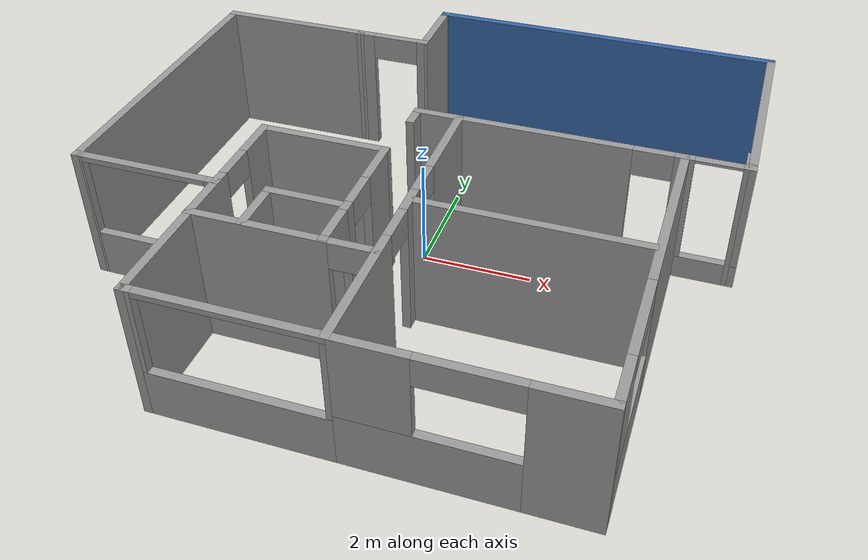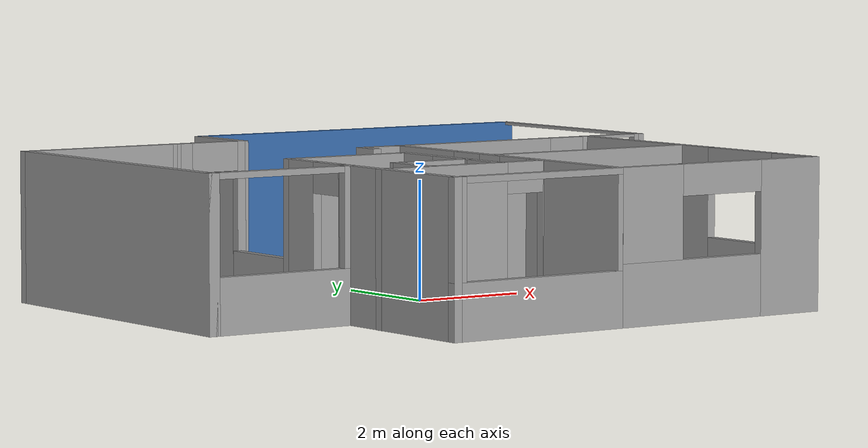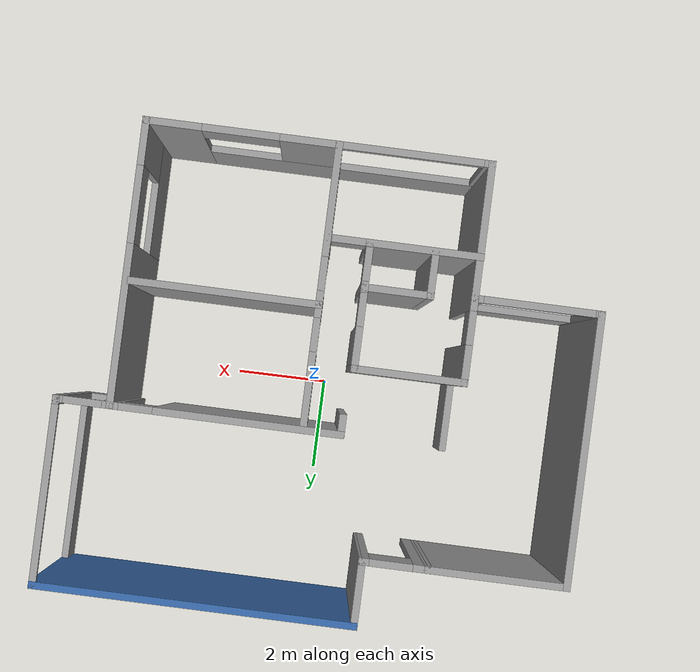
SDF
<?xml version='1.0'?>
<sdf version='1.7'>
  <model name='Myhouse'>
    <link name='Wall_0'>
      <pose>2.10158 4.8407 0 0 -0 0</pose>
      <self_collide>0</self_collide>
      <enable_wind>0</enable_wind>
      <kinematic>0</kinematic>
      <visual name='Wall_0_Visual'>
        <pose>0 0 1.25 0 -0 0</pose>
        <geometry>
          <box>
            <size>6.75 0.15 2.5</size>
          </box>
        </geometry>
        <material>
          <script>
            <uri>file://media/materials/scripts/gazebo.material</uri>
            <name>Gazebo/Grey</name>
          </script>
          <ambient>0.203922 0.396078 0.643137 1</ambient>
          <shader type='pixel'/>
        </material>
        <meta>
          <layer>0</layer>
        </meta>
        <transparency>0</transparency>
        <cast_shadows>1</cast_shadows>
      </visual>
      <collision name='Wall_0_Collision'>
        <laser_retro>0</laser_retro>
        <max_contacts>10</max_contacts>
        <pose>0 0 1.25 0 -0 0</pose>
        <geometry>
          <box>
            <size>6.75 0.15 2.5</size>
          </box>
        </geometry>
        <surface>
          <friction>
            <ode>
              <mu>1</mu>
              <mu2>1</mu2>
              <fdir1>0 0 0</fdir1>
              <slip1>0</slip1>
              <slip2>0</slip2>
            </ode>
            <torsional>
              <coefficient>1</coefficient>
              <patch_radius>0</patch_radius>
              <surface_radius>0</surface_radius>
              <use_patch_radius>1</use_patch_radius>
              <ode>
                <slip>0</slip>
              </ode>
            </torsional>
          </friction>
          <bounce>
            <restitution_coefficient>0</restitution_coefficient>
            <threshold>1e+06</threshold>
          </bounce>
          <contact>
            <collide_without_contact>0</collide_without_contact>
            <collide_without_contact_bitmask>1</collide_without_contact_bitmask>
            <collide_bitmask>1</collide_bitmask>
            <ode>
              <soft_cfm>0</soft_cfm>
              <soft_erp>0.2</soft_erp>
              <kp>1e+13</kp>
              <kd>1</kd>
              <max_vel>0.01</max_vel>
              <min_depth>0</min_depth>
            </ode>
            <bullet>
              <split_impulse>1</split_impulse>
              <split_impulse_penetration_threshold>-0.01</split_impulse_penetration_threshold>
              <soft_cfm>0</soft_cfm>
              <soft_erp>0.2</soft_erp>
              <kp>1e+13</kp>
              <kd>1</kd>
            </bullet>
          </contact>
        </surface>
      </collision>
    </link>
    <link name='Wall_1'>
      <pose>5.39997 2.92495 0 0 0 -1.57164</pose>
      <self_collide>0</self_collide>
      <enable_wind>0</enable_wind>
      <kinematic>0</kinematic>
      <visual name='Wall_1_Visual_0'>
        <pose>-1.94391 0 1.25 0 -0 0</pose>
        <geometry>
          <box>
            <size>0.093734 0.15 2.5</size>
          </box>
        </geometry>
        <material>
          <script>
            <uri>file://media/materials/scripts/gazebo.material</uri>
            <name>Gazebo/Grey</name>
          </script>
          <ambient>1 1 1 1</ambient>
          <shader type='pixel'/>
        </material>
        <meta>
          <layer>0</layer>
        </meta>
        <transparency>0</transparency>
        <cast_shadows>1</cast_shadows>
      </visual>
      <visual name='Wall_1_Visual_1'>
        <pose>0.046867 0 0.225 0 -0 0</pose>
        <geometry>
          <box>
            <size>3.88783 0.15 0.45</size>
          </box>
        </geometry>
        <material>
          <script>
            <uri>file://media/materials/scripts/gazebo.material</uri>
            <name>Gazebo/Grey</name>
          </script>
          <ambient>1 1 1 1</ambient>
          <shader type='pixel'/>
        </material>
        <meta>
          <layer>0</layer>
        </meta>
        <transparency>0</transparency>
        <cast_shadows>1</cast_shadows>
      </visual>
      <visual name='Wall_1_Visual_2'>
        <pose>1.89687 0 1.475 0 -0 0</pose>
        <geometry>
          <box>
            <size>0.187826 0.15 2.05</size>
          </box>
        </geometry>
        <material>
          <script>
            <uri>file://media/materials/scripts/gazebo.material</uri>
            <name>Gazebo/Grey</name>
          </script>
          <ambient>1 1 1 1</ambient>
          <shader type='pixel'/>
        </material>
        <meta>
          <layer>0</layer>
        </meta>
        <transparency>0</transparency>
        <cast_shadows>1</cast_shadows>
      </visual>
      <visual name='Wall_1_Visual_3'>
        <pose>-0.047046 0 2.475 0 -0 0</pose>
        <geometry>
          <box>
            <size>3.7 0.15 0.05</size>
          </box>
        </geometry>
        <material>
          <script>
            <uri>file://media/materials/scripts/gazebo.material</uri>
            <name>Gazebo/Grey</name>
          </script>
          <ambient>1 1 1 1</ambient>
          <shader type='pixel'/>
        </material>
        <meta>
          <layer>0</layer>
        </meta>
        <transparency>0</transparency>
        <cast_shadows>1</cast_shadows>
      </visual>
      <collision name='Wall_1_Collision_0'>
        <laser_retro>0</laser_retro>
        <max_contacts>10</max_contacts>
        <pose>-1.94391 0 1.25 0 -0 0</pose>
        <geometry>
          <box>
            <size>0.093734 0.15 2.5</size>
          </box>
        </geometry>
        <surface>
          <friction>
            <ode>
              <mu>1</mu>
              <mu2>1</mu2>
              <fdir1>0 0 0</fdir1>
              <slip1>0</slip1>
              <slip2>0</slip2>
            </ode>
            <torsional>
              <coefficient>1</coefficient>
              <patch_radius>0</patch_radius>
              <surface_radius>0</surface_radius>
              <use_patch_radius>1</use_patch_radius>
              <ode>
                <slip>0</slip>
              </ode>
            </torsional>
          </friction>
          <bounce>
            <restitution_coefficient>0</restitution_coefficient>
            <threshold>1e+06</threshold>
          </bounce>
          <contact>
            <collide_without_contact>0</collide_without_contact>
            <collide_without_contact_bitmask>1</collide_without_contact_bitmask>
            <collide_bitmask>1</collide_bitmask>
            <ode>
              <soft_cfm>0</soft_cfm>
              <soft_erp>0.2</soft_erp>
              <kp>1e+13</kp>
              <kd>1</kd>
              <max_vel>0.01</max_vel>
              <min_depth>0</min_depth>
            </ode>
            <bullet>
              <split_impulse>1</split_impulse>
              <split_impulse_penetration_threshold>-0.01</split_impulse_penetration_threshold>
              <soft_cfm>0</soft_cfm>
              <soft_erp>0.2</soft_erp>
              <kp>1e+13</kp>
              <kd>1</kd>
            </bullet>
          </contact>
        </surface>
      </collision>
      <collision name='Wall_1_Collision_1'>
        <laser_retro>0</laser_retro>
        <max_contacts>10</max_contacts>
        <pose>0.046867 0 0.225 0 -0 0</pose>
        <geometry>
          <box>
            <size>3.88783 0.15 0.45</size>
          </box>
        </geometry>
        <surface>
          <friction>
            <ode>
              <mu>1</mu>
              <mu2>1</mu2>
              <fdir1>0 0 0</fdir1>
              <slip1>0</slip1>
              <slip2>0</slip2>
            </ode>
            <torsional>
              <coefficient>1</coefficient>
              <patch_radius>0</patch_radius>
              <surface_radius>0</surface_radius>
              <use_patch_radius>1</use_patch_radius>
              <ode>
                <slip>0</slip>
              </ode>
            </torsional>
          </friction>
          <bounce>
            <restitution_coefficient>0</restitution_coefficient>
            <threshold>1e+06</threshold>
          </bounce>
          <contact>
            <collide_without_contact>0</collide_without_contact>
            <collide_without_contact_bitmask>1</collide_without_contact_bitmask>
            <collide_bitmask>1</collide_bitmask>
            <ode>
              <soft_cfm>0</soft_cfm>
              <soft_erp>0.2</soft_erp>
              <kp>1e+13</kp>
              <kd>1</kd>
              <max_vel>0.01</max_vel>
              <min_depth>0</min_depth>
            </ode>
            <bullet>
              <split_impulse>1</split_impulse>
              <split_impulse_penetration_threshold>-0.01</split_impulse_penetration_threshold>
              <soft_cfm>0</soft_cfm>
              <soft_erp>0.2</soft_erp>
              <kp>1e+13</kp>
              <kd>1</kd>
            </bullet>
          </contact>
        </surface>
      </collision>
      <collision name='Wall_1_Collision_2'>
        <laser_retro>0</laser_retro>
        <max_contacts>10</max_contacts>
        <pose>1.89687 0 1.475 0 -0 0</pose>
        <geometry>
          <box>
            <size>0.187826 0.15 2.05</size>
          </box>
        </geometry>
        <surface>
          <friction>
            <ode>
              <mu>1</mu>
              <mu2>1</mu2>
              <fdir1>0 0 0</fdir1>
              <slip1>0</slip1>
              <slip2>0</slip2>
            </ode>
            <torsional>
              <coefficient>1</coefficient>
              <patch_radius>0</patch_radius>
              <surface_radius>0</surface_radius>
              <use_patch_radius>1</use_patch_radius>
              <ode>
                <slip>0</slip>
              </ode>
            </torsional>
          </friction>
          <bounce>
            <restitution_coefficient>0</restitution_coefficient>
            <threshold>1e+06</threshold>
          </bounce>
          <contact>
            <collide_without_contact>0</collide_without_contact>
            <collide_without_contact_bitmask>1</collide_without_contact_bitmask>
            <collide_bitmask>1</collide_bitmask>
            <ode>
              <soft_cfm>0</soft_cfm>
              <soft_erp>0.2</soft_erp>
              <kp>1e+13</kp>
              <kd>1</kd>
              <max_vel>0.01</max_vel>
              <min_depth>0</min_depth>
            </ode>
            <bullet>
              <split_impulse>1</split_impulse>
              <split_impulse_penetration_threshold>-0.01</split_impulse_penetration_threshold>
              <soft_cfm>0</soft_cfm>
              <soft_erp>0.2</soft_erp>
              <kp>1e+13</kp>
              <kd>1</kd>
            </bullet>
          </contact>
        </surface>
      </collision>
      <collision name='Wall_1_Collision_3'>
        <laser_retro>0</laser_retro>
        <max_contacts>10</max_contacts>
        <pose>-0.047046 0 2.475 0 -0 0</pose>
        <geometry>
          <box>
            <size>3.7 0.15 0.05</size>
          </box>
        </geometry>
        <surface>
          <friction>
            <ode>
              <mu>1</mu>
              <mu2>1</mu2>
              <fdir1>0 0 0</fdir1>
              <slip1>0</slip1>
              <slip2>0</slip2>
            </ode>
            <torsional>
              <coefficient>1</coefficient>
              <patch_radius>0</patch_radius>
              <surface_radius>0</surface_radius>
              <use_patch_radius>1</use_patch_radius>
              <ode>
                <slip>0</slip>
              </ode>
            </torsional>
          </friction>
          <bounce>
            <restitution_coefficient>0</restitution_coefficient>
            <threshold>1e+06</threshold>
          </bounce>
          <contact>
            <collide_without_contact>0</collide_without_contact>
            <collide_without_contact_bitmask>1</collide_without_contact_bitmask>
            <collide_bitmask>1</collide_bitmask>
            <ode>
              <soft_cfm>0</soft_cfm>
              <soft_erp>0.2</soft_erp>
              <kp>1e+13</kp>
              <kd>1</kd>
              <max_vel>0.01</max_vel>
              <min_depth>0</min_depth>
            </ode>
            <bullet>
              <split_impulse>1</split_impulse>
              <split_impulse_penetration_threshold>-0.01</split_impulse_penetration_threshold>
              <soft_cfm>0</soft_cfm>
              <soft_erp>0.2</soft_erp>
              <kp>1e+13</kp>
              <kd>1</kd>
            </bullet>
          </contact>
        </surface>
      </collision>
    </link>
    <link name='Wall_13'>
      <pose>1.92675 1.00921 0 0 -0 3.14159</pose>
      <self_collide>0</self_collide>
      <enable_wind>0</enable_wind>
      <kinematic>0</kinematic>
      <visual name='Wall_13_Visual_0'>
        <pose>-2.32196 0 1.25 0 -0 0</pose>
        <geometry>
          <box>
            <size>0.249291 0.15 2.5</size>
          </box>
        </geometry>
        <material>
          <script>
            <uri>file://media/materials/scripts/gazebo.material</uri>
            <name>Gazebo/Grey</name>
          </script>
          <ambient>1 1 1 1</ambient>
          <shader type='pixel'/>
        </material>
        <meta>
          <layer>0</layer>
        </meta>
        <transparency>0</transparency>
        <cast_shadows>1</cast_shadows>
      </visual>
      <visual name='Wall_13_Visual_1'>
        <pose>0.474646 0 1.25 0 -0 0</pose>
        <geometry>
          <box>
            <size>3.94392 0.15 2.5</size>
          </box>
        </geometry>
        <material>
          <script>
            <uri>file://media/materials/scripts/gazebo.material</uri>
            <name>Gazebo/Grey</name>
          </script>
          <ambient>1 1 1 1</ambient>
          <shader type='pixel'/>
        </material>
        <meta>
          <layer>0</layer>
        </meta>
        <transparency>0</transparency>
        <cast_shadows>1</cast_shadows>
      </visual>
      <visual name='Wall_13_Visual_2'>
        <pose>-1.84732 0 2.25 0 -0 0</pose>
        <geometry>
          <box>
            <size>0.7 0.15 0.5</size>
          </box>
        </geometry>
        <material>
          <script>
            <uri>file://media/materials/scripts/gazebo.material</uri>
            <name>Gazebo/Grey</name>
          </script>
          <ambient>1 1 1 1</ambient>
          <shader type='pixel'/>
        </material>
        <meta>
          <layer>0</layer>
        </meta>
        <transparency>0</transparency>
        <cast_shadows>1</cast_shadows>
      </visual>
      <collision name='Wall_13_Collision_0'>
        <laser_retro>0</laser_retro>
        <max_contacts>10</max_contacts>
        <pose>-2.32196 0 1.25 0 -0 0</pose>
        <geometry>
          <box>
            <size>0.249291 0.15 2.5</size>
          </box>
        </geometry>
        <surface>
          <friction>
            <ode>
              <mu>1</mu>
              <mu2>1</mu2>
              <fdir1>0 0 0</fdir1>
              <slip1>0</slip1>
              <slip2>0</slip2>
            </ode>
            <torsional>
              <coefficient>1</coefficient>
              <patch_radius>0</patch_radius>
              <surface_radius>0</surface_radius>
              <use_patch_radius>1</use_patch_radius>
              <ode>
                <slip>0</slip>
              </ode>
            </torsional>
          </friction>
          <bounce>
            <restitution_coefficient>0</restitution_coefficient>
            <threshold>1e+06</threshold>
          </bounce>
          <contact>
            <collide_without_contact>0</collide_without_contact>
            <collide_without_contact_bitmask>1</collide_without_contact_bitmask>
            <collide_bitmask>1</collide_bitmask>
            <ode>
              <soft_cfm>0</soft_cfm>
              <soft_erp>0.2</soft_erp>
              <kp>1e+13</kp>
              <kd>1</kd>
              <max_vel>0.01</max_vel>
              <min_depth>0</min_depth>
            </ode>
            <bullet>
              <split_impulse>1</split_impulse>
              <split_impulse_penetration_threshold>-0.01</split_impulse_penetration_threshold>
              <soft_cfm>0</soft_cfm>
              <soft_erp>0.2</soft_erp>
              <kp>1e+13</kp>
              <kd>1</kd>
            </bullet>
          </contact>
        </surface>
      </collision>
      <collision name='Wall_13_Collision_1'>
        <laser_retro>0</laser_retro>
        <max_contacts>10</max_contacts>
        <pose>0.474646 0 1.25 0 -0 0</pose>
        <geometry>
          <box>
            <size>3.94392 0.15 2.5</size>
          </box>
        </geometry>
        <surface>
          <friction>
            <ode>
              <mu>1</mu>
              <mu2>1</mu2>
              <fdir1>0 0 0</fdir1>
              <slip1>0</slip1>
              <slip2>0</slip2>
            </ode>
            <torsional>
              <coefficient>1</coefficient>
              <patch_radius>0</patch_radius>
              <surface_radius>0</surface_radius>
              <use_patch_radius>1</use_patch_radius>
              <ode>
                <slip>0</slip>
              </ode>
            </torsional>
          </friction>
          <bounce>
            <restitution_coefficient>0</restitution_coefficient>
            <threshold>1e+06</threshold>
          </bounce>
          <contact>
            <collide_without_contact>0</collide_without_contact>
            <collide_without_contact_bitmask>1</collide_without_contact_bitmask>
            <collide_bitmask>1</collide_bitmask>
            <ode>
              <soft_cfm>0</soft_cfm>
              <soft_erp>0.2</soft_erp>
              <kp>1e+13</kp>
              <kd>1</kd>
              <max_vel>0.01</max_vel>
              <min_depth>0</min_depth>
            </ode>
            <bullet>
              <split_impulse>1</split_impulse>
              <split_impulse_penetration_threshold>-0.01</split_impulse_penetration_threshold>
              <soft_cfm>0</soft_cfm>
              <soft_erp>0.2</soft_erp>
              <kp>1e+13</kp>
              <kd>1</kd>
            </bullet>
          </contact>
        </surface>
      </collision>
      <collision name='Wall_13_Collision_2'>
        <laser_retro>0</laser_retro>
        <max_contacts>10</max_contacts>
        <pose>-1.84732 0 2.25 0 -0 0</pose>
        <geometry>
          <box>
            <size>0.7 0.15 0.5</size>
          </box>
        </geometry>
        <surface>
          <friction>
            <ode>
              <mu>1</mu>
              <mu2>1</mu2>
              <fdir1>0 0 0</fdir1>
              <slip1>0</slip1>
              <slip2>0</slip2>
            </ode>
            <torsional>
              <coefficient>1</coefficient>
              <patch_radius>0</patch_radius>
              <surface_radius>0</surface_radius>
              <use_patch_radius>1</use_patch_radius>
              <ode>
                <slip>0</slip>
              </ode>
            </torsional>
          </friction>
          <bounce>
            <restitution_coefficient>0</restitution_coefficient>
            <threshold>1e+06</threshold>
          </bounce>
          <contact>
            <collide_without_contact>0</collide_without_contact>
            <collide_without_contact_bitmask>1</collide_without_contact_bitmask>
            <collide_bitmask>1</collide_bitmask>
            <ode>
              <soft_cfm>0</soft_cfm>
              <soft_erp>0.2</soft_erp>
              <kp>1e+13</kp>
              <kd>1</kd>
              <max_vel>0.01</max_vel>
              <min_depth>0</min_depth>
            </ode>
            <bullet>
              <split_impulse>1</split_impulse>
              <split_impulse_penetration_threshold>-0.01</split_impulse_penetration_threshold>
              <soft_cfm>0</soft_cfm>
              <soft_erp>0.2</soft_erp>
              <kp>1e+13</kp>
              <kd>1</kd>
            </bullet>
          </contact>
        </surface>
      </collision>
    </link>
    <link name='Wall_17'>
      <pose>2.26458 -1.5613 0 0 -0 3.14159</pose>
      <self_collide>0</self_collide>
      <enable_wind>0</enable_wind>
      <kinematic>0</kinematic>
      <visual name='Wall_17_Visual'>
        <pose>0 0 1.25 0 -0 0</pose>
        <geometry>
          <box>
            <size>4 0.15 2.5</size>
          </box>
        </geometry>
        <material>
          <script>
            <uri>file://media/materials/scripts/gazebo.material</uri>
            <name>Gazebo/Grey</name>
          </script>
          <ambient>1 1 1 1</ambient>
          <shader type='pixel'/>
        </material>
        <meta>
          <layer>0</layer>
        </meta>
        <transparency>0</transparency>
        <cast_shadows>1</cast_shadows>
      </visual>
      <collision name='Wall_17_Collision'>
        <laser_retro>0</laser_retro>
        <max_contacts>10</max_contacts>
        <pose>0 0 1.25 0 -0 0</pose>
        <geometry>
          <box>
            <size>4 0.15 2.5</size>
          </box>
        </geometry>
        <surface>
          <friction>
            <ode>
              <mu>1</mu>
              <mu2>1</mu2>
              <fdir1>0 0 0</fdir1>
              <slip1>0</slip1>
              <slip2>0</slip2>
            </ode>
            <torsional>
              <coefficient>1</coefficient>
              <patch_radius>0</patch_radius>
              <surface_radius>0</surface_radius>
              <use_patch_radius>1</use_patch_radius>
              <ode>
                <slip>0</slip>
              </ode>
            </torsional>
          </friction>
          <bounce>
            <restitution_coefficient>0</restitution_coefficient>
            <threshold>1e+06</threshold>
          </bounce>
          <contact>
            <collide_without_contact>0</collide_without_contact>
            <collide_without_contact_bitmask>1</collide_without_contact_bitmask>
            <collide_bitmask>1</collide_bitmask>
            <ode>
              <soft_cfm>0</soft_cfm>
              <soft_erp>0.2</soft_erp>
              <kp>1e+13</kp>
              <kd>1</kd>
              <max_vel>0.01</max_vel>
              <min_depth>0</min_depth>
            </ode>
            <bullet>
              <split_impulse>1</split_impulse>
              <split_impulse_penetration_threshold>-0.01</split_impulse_penetration_threshold>
              <soft_cfm>0</soft_cfm>
              <soft_erp>0.2</soft_erp>
              <kp>1e+13</kp>
              <kd>1</kd>
            </bullet>
          </contact>
        </surface>
      </collision>
    </link>
    <link name='Wall_23'>
      <pose>0.334124 -1.9144 0 0 -0 1.5708</pose>
      <self_collide>0</self_collide>
      <enable_wind>0</enable_wind>
      <kinematic>0</kinematic>
      <visual name='Wall_23_Visual_0'>
        <pose>-1.81879 0 1.25 0 -0 0</pose>
        <geometry>
          <box>
            <size>2.36243 0.15 2.5</size>
          </box>
        </geometry>
        <material>
          <script>
            <uri>file://media/materials/scripts/gazebo.material</uri>
            <name>Gazebo/Grey</name>
          </script>
          <ambient>1 1 1 1</ambient>
          <shader type='pixel'/>
        </material>
        <meta>
          <layer>0</layer>
        </meta>
        <transparency>0</transparency>
        <cast_shadows>1</cast_shadows>
      </visual>
      <visual name='Wall_23_Visual_1'>
        <pose>0.340045 0 1.25 0 -0 0</pose>
        <geometry>
          <box>
            <size>0.555232 0.15 2.5</size>
          </box>
        </geometry>
        <material>
          <script>
            <uri>file://media/materials/scripts/gazebo.material</uri>
            <name>Gazebo/Grey</name>
          </script>
          <ambient>1 1 1 1</ambient>
          <shader type='pixel'/>
        </material>
        <meta>
          <layer>0</layer>
        </meta>
        <transparency>0</transparency>
        <cast_shadows>1</cast_shadows>
      </visual>
      <visual name='Wall_23_Visual_2'>
        <pose>2.15883 0 1.25 0 -0 0</pose>
        <geometry>
          <box>
            <size>1.68234 0.15 2.5</size>
          </box>
        </geometry>
        <material>
          <script>
            <uri>file://media/materials/scripts/gazebo.material</uri>
            <name>Gazebo/Grey</name>
          </script>
          <ambient>1 1 1 1</ambient>
          <shader type='pixel'/>
        </material>
        <meta>
          <layer>0</layer>
        </meta>
        <transparency>0</transparency>
        <cast_shadows>1</cast_shadows>
      </visual>
      <visual name='Wall_23_Visual_3'>
        <pose>-0.287571 0 2.25 0 -0 0</pose>
        <geometry>
          <box>
            <size>0.7 0.15 0.5</size>
          </box>
        </geometry>
        <material>
          <script>
            <uri>file://media/materials/scripts/gazebo.material</uri>
            <name>Gazebo/Grey</name>
          </script>
          <ambient>1 1 1 1</ambient>
          <shader type='pixel'/>
        </material>
        <meta>
          <layer>0</layer>
        </meta>
        <transparency>0</transparency>
        <cast_shadows>1</cast_shadows>
      </visual>
      <visual name='Wall_23_Visual_4'>
        <pose>0.967661 0 2.25 0 -0 0</pose>
        <geometry>
          <box>
            <size>0.7 0.15 0.5</size>
          </box>
        </geometry>
        <material>
          <script>
            <uri>file://media/materials/scripts/gazebo.material</uri>
            <name>Gazebo/Grey</name>
          </script>
          <ambient>1 1 1 1</ambient>
          <shader type='pixel'/>
        </material>
        <meta>
          <layer>0</layer>
        </meta>
        <transparency>0</transparency>
        <cast_shadows>1</cast_shadows>
      </visual>
      <collision name='Wall_23_Collision_0'>
        <laser_retro>0</laser_retro>
        <max_contacts>10</max_contacts>
        <pose>-1.81879 0 1.25 0 -0 0</pose>
        <geometry>
          <box>
            <size>2.36243 0.15 2.5</size>
          </box>
        </geometry>
        <surface>
          <friction>
            <ode>
              <mu>1</mu>
              <mu2>1</mu2>
              <fdir1>0 0 0</fdir1>
              <slip1>0</slip1>
              <slip2>0</slip2>
            </ode>
            <torsional>
              <coefficient>1</coefficient>
              <patch_radius>0</patch_radius>
              <surface_radius>0</surface_radius>
              <use_patch_radius>1</use_patch_radius>
              <ode>
                <slip>0</slip>
              </ode>
            </torsional>
          </friction>
          <bounce>
            <restitution_coefficient>0</restitution_coefficient>
            <threshold>1e+06</threshold>
          </bounce>
          <contact>
            <collide_without_contact>0</collide_without_contact>
            <collide_without_contact_bitmask>1</collide_without_contact_bitmask>
            <collide_bitmask>1</collide_bitmask>
            <ode>
              <soft_cfm>0</soft_cfm>
              <soft_erp>0.2</soft_erp>
              <kp>1e+13</kp>
              <kd>1</kd>
              <max_vel>0.01</max_vel>
              <min_depth>0</min_depth>
            </ode>
            <bullet>
              <split_impulse>1</split_impulse>
              <split_impulse_penetration_threshold>-0.01</split_impulse_penetration_threshold>
              <soft_cfm>0</soft_cfm>
              <soft_erp>0.2</soft_erp>
              <kp>1e+13</kp>
              <kd>1</kd>
            </bullet>
          </contact>
        </surface>
      </collision>
      <collision name='Wall_23_Collision_1'>
        <laser_retro>0</laser_retro>
        <max_contacts>10</max_contacts>
        <pose>0.340045 0 1.25 0 -0 0</pose>
        <geometry>
          <box>
            <size>0.555232 0.15 2.5</size>
          </box>
        </geometry>
        <surface>
          <friction>
            <ode>
              <mu>1</mu>
              <mu2>1</mu2>
              <fdir1>0 0 0</fdir1>
              <slip1>0</slip1>
              <slip2>0</slip2>
            </ode>
            <torsional>
              <coefficient>1</coefficient>
              <patch_radius>0</patch_radius>
              <surface_radius>0</surface_radius>
              <use_patch_radius>1</use_patch_radius>
              <ode>
                <slip>0</slip>
              </ode>
            </torsional>
          </friction>
          <bounce>
            <restitution_coefficient>0</restitution_coefficient>
            <threshold>1e+06</threshold>
          </bounce>
          <contact>
            <collide_without_contact>0</collide_without_contact>
            <collide_without_contact_bitmask>1</collide_without_contact_bitmask>
            <collide_bitmask>1</collide_bitmask>
            <ode>
              <soft_cfm>0</soft_cfm>
              <soft_erp>0.2</soft_erp>
              <kp>1e+13</kp>
              <kd>1</kd>
              <max_vel>0.01</max_vel>
              <min_depth>0</min_depth>
            </ode>
            <bullet>
              <split_impulse>1</split_impulse>
              <split_impulse_penetration_threshold>-0.01</split_impulse_penetration_threshold>
              <soft_cfm>0</soft_cfm>
              <soft_erp>0.2</soft_erp>
              <kp>1e+13</kp>
              <kd>1</kd>
            </bullet>
          </contact>
        </surface>
      </collision>
      <collision name='Wall_23_Collision_2'>
        <laser_retro>0</laser_retro>
        <max_contacts>10</max_contacts>
        <pose>2.15883 0 1.25 0 -0 0</pose>
        <geometry>
          <box>
            <size>1.68234 0.15 2.5</size>
          </box>
        </geometry>
        <surface>
          <friction>
            <ode>
              <mu>1</mu>
              <mu2>1</mu2>
              <fdir1>0 0 0</fdir1>
              <slip1>0</slip1>
              <slip2>0</slip2>
            </ode>
            <torsional>
              <coefficient>1</coefficient>
              <patch_radius>0</patch_radius>
              <surface_radius>0</surface_radius>
              <use_patch_radius>1</use_patch_radius>
              <ode>
                <slip>0</slip>
              </ode>
            </torsional>
          </friction>
          <bounce>
            <restitution_coefficient>0</restitution_coefficient>
            <threshold>1e+06</threshold>
          </bounce>
          <contact>
            <collide_without_contact>0</collide_without_contact>
            <collide_without_contact_bitmask>1</collide_without_contact_bitmask>
            <collide_bitmask>1</collide_bitmask>
            <ode>
              <soft_cfm>0</soft_cfm>
              <soft_erp>0.2</soft_erp>
              <kp>1e+13</kp>
              <kd>1</kd>
              <max_vel>0.01</max_vel>
              <min_depth>0</min_depth>
            </ode>
            <bullet>
              <split_impulse>1</split_impulse>
              <split_impulse_penetration_threshold>-0.01</split_impulse_penetration_threshold>
              <soft_cfm>0</soft_cfm>
              <soft_erp>0.2</soft_erp>
              <kp>1e+13</kp>
              <kd>1</kd>
            </bullet>
          </contact>
        </surface>
      </collision>
      <collision name='Wall_23_Collision_3'>
        <laser_retro>0</laser_retro>
        <max_contacts>10</max_contacts>
        <pose>-0.287571 0 2.25 0 -0 0</pose>
        <geometry>
          <box>
            <size>0.7 0.15 0.5</size>
          </box>
        </geometry>
        <surface>
          <friction>
            <ode>
              <mu>1</mu>
              <mu2>1</mu2>
              <fdir1>0 0 0</fdir1>
              <slip1>0</slip1>
              <slip2>0</slip2>
            </ode>
            <torsional>
              <coefficient>1</coefficient>
              <patch_radius>0</patch_radius>
              <surface_radius>0</surface_radius>
              <use_patch_radius>1</use_patch_radius>
              <ode>
                <slip>0</slip>
              </ode>
            </torsional>
          </friction>
          <bounce>
            <restitution_coefficient>0</restitution_coefficient>
            <threshold>1e+06</threshold>
          </bounce>
          <contact>
            <collide_without_contact>0</collide_without_contact>
            <collide_without_contact_bitmask>1</collide_without_contact_bitmask>
            <collide_bitmask>1</collide_bitmask>
            <ode>
              <soft_cfm>0</soft_cfm>
              <soft_erp>0.2</soft_erp>
              <kp>1e+13</kp>
              <kd>1</kd>
              <max_vel>0.01</max_vel>
              <min_depth>0</min_depth>
            </ode>
            <bullet>
              <split_impulse>1</split_impulse>
              <split_impulse_penetration_threshold>-0.01</split_impulse_penetration_threshold>
              <soft_cfm>0</soft_cfm>
              <soft_erp>0.2</soft_erp>
              <kp>1e+13</kp>
              <kd>1</kd>
            </bullet>
          </contact>
        </surface>
      </collision>
      <collision name='Wall_23_Collision_4'>
        <laser_retro>0</laser_retro>
        <max_contacts>10</max_contacts>
        <pose>0.967661 0 2.25 0 -0 0</pose>
        <geometry>
          <box>
            <size>0.7 0.15 0.5</size>
          </box>
        </geometry>
        <surface>
          <friction>
            <ode>
              <mu>1</mu>
              <mu2>1</mu2>
              <fdir1>0 0 0</fdir1>
              <slip1>0</slip1>
              <slip2>0</slip2>
            </ode>
            <torsional>
              <coefficient>1</coefficient>
              <patch_radius>0</patch_radius>
              <surface_radius>0</surface_radius>
              <use_patch_radius>1</use_patch_radius>
              <ode>
                <slip>0</slip>
              </ode>
            </torsional>
          </friction>
          <bounce>
            <restitution_coefficient>0</restitution_coefficient>
            <threshold>1e+06</threshold>
          </bounce>
          <contact>
            <collide_without_contact>0</collide_without_contact>
            <collide_without_contact_bitmask>1</collide_without_contact_bitmask>
            <collide_bitmask>1</collide_bitmask>
            <ode>
              <soft_cfm>0</soft_cfm>
              <soft_erp>0.2</soft_erp>
              <kp>1e+13</kp>
              <kd>1</kd>
              <max_vel>0.01</max_vel>
              <min_depth>0</min_depth>
            </ode>
            <bullet>
              <split_impulse>1</split_impulse>
              <split_impulse_penetration_threshold>-0.01</split_impulse_penetration_threshold>
              <soft_cfm>0</soft_cfm>
              <soft_erp>0.2</soft_erp>
              <kp>1e+13</kp>
              <kd>1</kd>
            </bullet>
          </contact>
        </surface>
      </collision>
    </link>
    <link name='Wall_27'>
      <pose>-1.25954 -2.94166 0 0 -0 0</pose>
      <self_collide>0</self_collide>
      <enable_wind>0</enable_wind>
      <kinematic>0</kinematic>
      <visual name='Wall_27_Visual_0'>
        <pose>-0.409905 0 1.25 0 -0 0</pose>
        <geometry>
          <box>
            <size>2.43019 0.15 2.5</size>
          </box>
        </geometry>
        <material>
          <script>
            <uri>file://media/materials/scripts/gazebo.material</uri>
            <name>Gazebo/Grey</name>
          </script>
          <ambient>1 1 1 1</ambient>
          <shader type='pixel'/>
        </material>
        <meta>
          <layer>0</layer>
        </meta>
        <transparency>0</transparency>
        <cast_shadows>1</cast_shadows>
      </visual>
      <visual name='Wall_27_Visual_1'>
        <pose>1.56509 0 1.25 0 -0 0</pose>
        <geometry>
          <box>
            <size>0.119811 0.15 2.5</size>
          </box>
        </geometry>
        <material>
          <script>
            <uri>file://media/materials/scripts/gazebo.material</uri>
            <name>Gazebo/Grey</name>
          </script>
          <ambient>1 1 1 1</ambient>
          <shader type='pixel'/>
        </material>
        <meta>
          <layer>0</layer>
        </meta>
        <transparency>0</transparency>
        <cast_shadows>1</cast_shadows>
      </visual>
      <visual name='Wall_27_Visual_2'>
        <pose>1.15519 0 2.25 0 -0 0</pose>
        <geometry>
          <box>
            <size>0.7 0.15 0.5</size>
          </box>
        </geometry>
        <material>
          <script>
            <uri>file://media/materials/scripts/gazebo.material</uri>
            <name>Gazebo/Grey</name>
          </script>
          <ambient>1 1 1 1</ambient>
          <shader type='pixel'/>
        </material>
        <meta>
          <layer>0</layer>
        </meta>
        <transparency>0</transparency>
        <cast_shadows>1</cast_shadows>
      </visual>
      <collision name='Wall_27_Collision_0'>
        <laser_retro>0</laser_retro>
        <max_contacts>10</max_contacts>
        <pose>-0.409905 0 1.25 0 -0 0</pose>
        <geometry>
          <box>
            <size>2.43019 0.15 2.5</size>
          </box>
        </geometry>
        <surface>
          <friction>
            <ode>
              <mu>1</mu>
              <mu2>1</mu2>
              <fdir1>0 0 0</fdir1>
              <slip1>0</slip1>
              <slip2>0</slip2>
            </ode>
            <torsional>
              <coefficient>1</coefficient>
              <patch_radius>0</patch_radius>
              <surface_radius>0</surface_radius>
              <use_patch_radius>1</use_patch_radius>
              <ode>
                <slip>0</slip>
              </ode>
            </torsional>
          </friction>
          <bounce>
            <restitution_coefficient>0</restitution_coefficient>
            <threshold>1e+06</threshold>
          </bounce>
          <contact>
            <collide_without_contact>0</collide_without_contact>
            <collide_without_contact_bitmask>1</collide_without_contact_bitmask>
            <collide_bitmask>1</collide_bitmask>
            <ode>
              <soft_cfm>0</soft_cfm>
              <soft_erp>0.2</soft_erp>
              <kp>1e+13</kp>
              <kd>1</kd>
              <max_vel>0.01</max_vel>
              <min_depth>0</min_depth>
            </ode>
            <bullet>
              <split_impulse>1</split_impulse>
              <split_impulse_penetration_threshold>-0.01</split_impulse_penetration_threshold>
              <soft_cfm>0</soft_cfm>
              <soft_erp>0.2</soft_erp>
              <kp>1e+13</kp>
              <kd>1</kd>
            </bullet>
          </contact>
        </surface>
      </collision>
      <collision name='Wall_27_Collision_1'>
        <laser_retro>0</laser_retro>
        <max_contacts>10</max_contacts>
        <pose>1.56509 0 1.25 0 -0 0</pose>
        <geometry>
          <box>
            <size>0.119811 0.15 2.5</size>
          </box>
        </geometry>
        <surface>
          <friction>
            <ode>
              <mu>1</mu>
              <mu2>1</mu2>
              <fdir1>0 0 0</fdir1>
              <slip1>0</slip1>
              <slip2>0</slip2>
            </ode>
            <torsional>
              <coefficient>1</coefficient>
              <patch_radius>0</patch_radius>
              <surface_radius>0</surface_radius>
              <use_patch_radius>1</use_patch_radius>
              <ode>
                <slip>0</slip>
              </ode>
            </torsional>
          </friction>
          <bounce>
            <restitution_coefficient>0</restitution_coefficient>
            <threshold>1e+06</threshold>
          </bounce>
          <contact>
            <collide_without_contact>0</collide_without_contact>
            <collide_without_contact_bitmask>1</collide_without_contact_bitmask>
            <collide_bitmask>1</collide_bitmask>
            <ode>
              <soft_cfm>0</soft_cfm>
              <soft_erp>0.2</soft_erp>
              <kp>1e+13</kp>
              <kd>1</kd>
              <max_vel>0.01</max_vel>
              <min_depth>0</min_depth>
            </ode>
            <bullet>
              <split_impulse>1</split_impulse>
              <split_impulse_penetration_threshold>-0.01</split_impulse_penetration_threshold>
              <soft_cfm>0</soft_cfm>
              <soft_erp>0.2</soft_erp>
              <kp>1e+13</kp>
              <kd>1</kd>
            </bullet>
          </contact>
        </surface>
      </collision>
      <collision name='Wall_27_Collision_2'>
        <laser_retro>0</laser_retro>
        <max_contacts>10</max_contacts>
        <pose>1.15519 0 2.25 0 -0 0</pose>
        <geometry>
          <box>
            <size>0.7 0.15 0.5</size>
          </box>
        </geometry>
        <surface>
          <friction>
            <ode>
              <mu>1</mu>
              <mu2>1</mu2>
              <fdir1>0 0 0</fdir1>
              <slip1>0</slip1>
              <slip2>0</slip2>
            </ode>
            <torsional>
              <coefficient>1</coefficient>
              <patch_radius>0</patch_radius>
              <surface_radius>0</surface_radius>
              <use_patch_radius>1</use_patch_radius>
              <ode>
                <slip>0</slip>
              </ode>
            </torsional>
          </friction>
          <bounce>
            <restitution_coefficient>0</restitution_coefficient>
            <threshold>1e+06</threshold>
          </bounce>
          <contact>
            <collide_without_contact>0</collide_without_contact>
            <collide_without_contact_bitmask>1</collide_without_contact_bitmask>
            <collide_bitmask>1</collide_bitmask>
            <ode>
              <soft_cfm>0</soft_cfm>
              <soft_erp>0.2</soft_erp>
              <kp>1e+13</kp>
              <kd>1</kd>
              <max_vel>0.01</max_vel>
              <min_depth>0</min_depth>
            </ode>
            <bullet>
              <split_impulse>1</split_impulse>
              <split_impulse_penetration_threshold>-0.01</split_impulse_penetration_threshold>
              <soft_cfm>0</soft_cfm>
              <soft_erp>0.2</soft_erp>
              <kp>1e+13</kp>
              <kd>1</kd>
            </bullet>
          </contact>
        </surface>
      </collision>
    </link>
    <link name='Wall_33'>
      <pose>-0.546419 -1.6345 0 0 -0 1.5708</pose>
      <self_collide>0</self_collide>
      <enable_wind>0</enable_wind>
      <kinematic>0</kinematic>
      <visual name='Wall_33_Visual_0'>
        <pose>-1.28707 0 1.25 0 -0 0</pose>
        <geometry>
          <box>
            <size>0.129459 0.15 2.5</size>
          </box>
        </geometry>
        <material>
          <script>
            <uri>file://media/materials/scripts/gazebo.material</uri>
            <name>Gazebo/Grey</name>
          </script>
          <ambient>1 1 1 1</ambient>
          <shader type='pixel'/>
        </material>
        <meta>
          <layer>0</layer>
        </meta>
        <transparency>0</transparency>
        <cast_shadows>1</cast_shadows>
      </visual>
      <visual name='Wall_33_Visual_1'>
        <pose>-0.408085 0 1.25 0 -0 0</pose>
        <geometry>
          <box>
            <size>0.228511 0.15 2.5</size>
          </box>
        </geometry>
        <material>
          <script>
            <uri>file://media/materials/scripts/gazebo.material</uri>
            <name>Gazebo/Grey</name>
          </script>
          <ambient>1 1 1 1</ambient>
          <shader type='pixel'/>
        </material>
        <meta>
          <layer>0</layer>
        </meta>
        <transparency>0</transparency>
        <cast_shadows>1</cast_shadows>
      </visual>
      <visual name='Wall_33_Visual_2'>
        <pose>0.878985 0 1.25 0 -0 0</pose>
        <geometry>
          <box>
            <size>0.945628 0.15 2.5</size>
          </box>
        </geometry>
        <material>
          <script>
            <uri>file://media/materials/scripts/gazebo.material</uri>
            <name>Gazebo/Grey</name>
          </script>
          <ambient>1 1 1 1</ambient>
          <shader type='pixel'/>
        </material>
        <meta>
          <layer>0</layer>
        </meta>
        <transparency>0</transparency>
        <cast_shadows>1</cast_shadows>
      </visual>
      <visual name='Wall_33_Visual_3'>
        <pose>-0.87234 0 2.25 0 -0 0</pose>
        <geometry>
          <box>
            <size>0.7 0.15 0.5</size>
          </box>
        </geometry>
        <material>
          <script>
            <uri>file://media/materials/scripts/gazebo.material</uri>
            <name>Gazebo/Grey</name>
          </script>
          <ambient>1 1 1 1</ambient>
          <shader type='pixel'/>
        </material>
        <meta>
          <layer>0</layer>
        </meta>
        <transparency>0</transparency>
        <cast_shadows>1</cast_shadows>
      </visual>
      <visual name='Wall_33_Visual_4'>
        <pose>0.05617 0 2.25 0 -0 0</pose>
        <geometry>
          <box>
            <size>0.7 0.15 0.5</size>
          </box>
        </geometry>
        <material>
          <script>
            <uri>file://media/materials/scripts/gazebo.material</uri>
            <name>Gazebo/Grey</name>
          </script>
          <ambient>1 1 1 1</ambient>
          <shader type='pixel'/>
        </material>
        <meta>
          <layer>0</layer>
        </meta>
        <transparency>0</transparency>
        <cast_shadows>1</cast_shadows>
      </visual>
      <collision name='Wall_33_Collision_0'>
        <laser_retro>0</laser_retro>
        <max_contacts>10</max_contacts>
        <pose>-1.28707 0 1.25 0 -0 0</pose>
        <geometry>
          <box>
            <size>0.129459 0.15 2.5</size>
          </box>
        </geometry>
        <surface>
          <friction>
            <ode>
              <mu>1</mu>
              <mu2>1</mu2>
              <fdir1>0 0 0</fdir1>
              <slip1>0</slip1>
              <slip2>0</slip2>
            </ode>
            <torsional>
              <coefficient>1</coefficient>
              <patch_radius>0</patch_radius>
              <surface_radius>0</surface_radius>
              <use_patch_radius>1</use_patch_radius>
              <ode>
                <slip>0</slip>
              </ode>
            </torsional>
          </friction>
          <bounce>
            <restitution_coefficient>0</restitution_coefficient>
            <threshold>1e+06</threshold>
          </bounce>
          <contact>
            <collide_without_contact>0</collide_without_contact>
            <collide_without_contact_bitmask>1</collide_without_contact_bitmask>
            <collide_bitmask>1</collide_bitmask>
            <ode>
              <soft_cfm>0</soft_cfm>
              <soft_erp>0.2</soft_erp>
              <kp>1e+13</kp>
              <kd>1</kd>
              <max_vel>0.01</max_vel>
              <min_depth>0</min_depth>
            </ode>
            <bullet>
              <split_impulse>1</split_impulse>
              <split_impulse_penetration_threshold>-0.01</split_impulse_penetration_threshold>
              <soft_cfm>0</soft_cfm>
              <soft_erp>0.2</soft_erp>
              <kp>1e+13</kp>
              <kd>1</kd>
            </bullet>
          </contact>
        </surface>
      </collision>
      <collision name='Wall_33_Collision_1'>
        <laser_retro>0</laser_retro>
        <max_contacts>10</max_contacts>
        <pose>-0.408085 0 1.25 0 -0 0</pose>
        <geometry>
          <box>
            <size>0.228511 0.15 2.5</size>
          </box>
        </geometry>
        <surface>
          <friction>
            <ode>
              <mu>1</mu>
              <mu2>1</mu2>
              <fdir1>0 0 0</fdir1>
              <slip1>0</slip1>
              <slip2>0</slip2>
            </ode>
            <torsional>
              <coefficient>1</coefficient>
              <patch_radius>0</patch_radius>
              <surface_radius>0</surface_radius>
              <use_patch_radius>1</use_patch_radius>
              <ode>
                <slip>0</slip>
              </ode>
            </torsional>
          </friction>
          <bounce>
            <restitution_coefficient>0</restitution_coefficient>
            <threshold>1e+06</threshold>
          </bounce>
          <contact>
            <collide_without_contact>0</collide_without_contact>
            <collide_without_contact_bitmask>1</collide_without_contact_bitmask>
            <collide_bitmask>1</collide_bitmask>
            <ode>
              <soft_cfm>0</soft_cfm>
              <soft_erp>0.2</soft_erp>
              <kp>1e+13</kp>
              <kd>1</kd>
              <max_vel>0.01</max_vel>
              <min_depth>0</min_depth>
            </ode>
            <bullet>
              <split_impulse>1</split_impulse>
              <split_impulse_penetration_threshold>-0.01</split_impulse_penetration_threshold>
              <soft_cfm>0</soft_cfm>
              <soft_erp>0.2</soft_erp>
              <kp>1e+13</kp>
              <kd>1</kd>
            </bullet>
          </contact>
        </surface>
      </collision>
      <collision name='Wall_33_Collision_2'>
        <laser_retro>0</laser_retro>
        <max_contacts>10</max_contacts>
        <pose>0.878985 0 1.25 0 -0 0</pose>
        <geometry>
          <box>
            <size>0.945628 0.15 2.5</size>
          </box>
        </geometry>
        <surface>
          <friction>
            <ode>
              <mu>1</mu>
              <mu2>1</mu2>
              <fdir1>0 0 0</fdir1>
              <slip1>0</slip1>
              <slip2>0</slip2>
            </ode>
            <torsional>
              <coefficient>1</coefficient>
              <patch_radius>0</patch_radius>
              <surface_radius>0</surface_radius>
              <use_patch_radius>1</use_patch_radius>
              <ode>
                <slip>0</slip>
              </ode>
            </torsional>
          </friction>
          <bounce>
            <restitution_coefficient>0</restitution_coefficient>
            <threshold>1e+06</threshold>
          </bounce>
          <contact>
            <collide_without_contact>0</collide_without_contact>
            <collide_without_contact_bitmask>1</collide_without_contact_bitmask>
            <collide_bitmask>1</collide_bitmask>
            <ode>
              <soft_cfm>0</soft_cfm>
              <soft_erp>0.2</soft_erp>
              <kp>1e+13</kp>
              <kd>1</kd>
              <max_vel>0.01</max_vel>
              <min_depth>0</min_depth>
            </ode>
            <bullet>
              <split_impulse>1</split_impulse>
              <split_impulse_penetration_threshold>-0.01</split_impulse_penetration_threshold>
              <soft_cfm>0</soft_cfm>
              <soft_erp>0.2</soft_erp>
              <kp>1e+13</kp>
              <kd>1</kd>
            </bullet>
          </contact>
        </surface>
      </collision>
      <collision name='Wall_33_Collision_3'>
        <laser_retro>0</laser_retro>
        <max_contacts>10</max_contacts>
        <pose>-0.87234 0 2.25 0 -0 0</pose>
        <geometry>
          <box>
            <size>0.7 0.15 0.5</size>
          </box>
        </geometry>
        <surface>
          <friction>
            <ode>
              <mu>1</mu>
              <mu2>1</mu2>
              <fdir1>0 0 0</fdir1>
              <slip1>0</slip1>
              <slip2>0</slip2>
            </ode>
            <torsional>
              <coefficient>1</coefficient>
              <patch_radius>0</patch_radius>
              <surface_radius>0</surface_radius>
              <use_patch_radius>1</use_patch_radius>
              <ode>
                <slip>0</slip>
              </ode>
            </torsional>
          </friction>
          <bounce>
            <restitution_coefficient>0</restitution_coefficient>
            <threshold>1e+06</threshold>
          </bounce>
          <contact>
            <collide_without_contact>0</collide_without_contact>
            <collide_without_contact_bitmask>1</collide_without_contact_bitmask>
            <collide_bitmask>1</collide_bitmask>
            <ode>
              <soft_cfm>0</soft_cfm>
              <soft_erp>0.2</soft_erp>
              <kp>1e+13</kp>
              <kd>1</kd>
              <max_vel>0.01</max_vel>
              <min_depth>0</min_depth>
            </ode>
            <bullet>
              <split_impulse>1</split_impulse>
              <split_impulse_penetration_threshold>-0.01</split_impulse_penetration_threshold>
              <soft_cfm>0</soft_cfm>
              <soft_erp>0.2</soft_erp>
              <kp>1e+13</kp>
              <kd>1</kd>
            </bullet>
          </contact>
        </surface>
      </collision>
      <collision name='Wall_33_Collision_4'>
        <laser_retro>0</laser_retro>
        <max_contacts>10</max_contacts>
        <pose>0.05617 0 2.25 0 -0 0</pose>
        <geometry>
          <box>
            <size>0.7 0.15 0.5</size>
          </box>
        </geometry>
        <surface>
          <friction>
            <ode>
              <mu>1</mu>
              <mu2>1</mu2>
              <fdir1>0 0 0</fdir1>
              <slip1>0</slip1>
              <slip2>0</slip2>
            </ode>
            <torsional>
              <coefficient>1</coefficient>
              <patch_radius>0</patch_radius>
              <surface_radius>0</surface_radius>
              <use_patch_radius>1</use_patch_radius>
              <ode>
                <slip>0</slip>
              </ode>
            </torsional>
          </friction>
          <bounce>
            <restitution_coefficient>0</restitution_coefficient>
            <threshold>1e+06</threshold>
          </bounce>
          <contact>
            <collide_without_contact>0</collide_without_contact>
            <collide_without_contact_bitmask>1</collide_without_contact_bitmask>
            <collide_bitmask>1</collide_bitmask>
            <ode>
              <soft_cfm>0</soft_cfm>
              <soft_erp>0.2</soft_erp>
              <kp>1e+13</kp>
              <kd>1</kd>
              <max_vel>0.01</max_vel>
              <min_depth>0</min_depth>
            </ode>
            <bullet>
              <split_impulse>1</split_impulse>
              <split_impulse_penetration_threshold>-0.01</split_impulse_penetration_threshold>
              <soft_cfm>0</soft_cfm>
              <soft_erp>0.2</soft_erp>
              <kp>1e+13</kp>
              <kd>1</kd>
            </bullet>
          </contact>
        </surface>
      </collision>
    </link>
    <link name='Wall_34'>
      <pose>-1.67392 -0.359359 0 0 -0 3.14115</pose>
      <self_collide>0</self_collide>
      <enable_wind>0</enable_wind>
      <kinematic>0</kinematic>
      <visual name='Wall_34_Visual'>
        <pose>0 0 1.25 0 -0 0</pose>
        <geometry>
          <box>
            <size>2.40523 0.15 2.5</size>
          </box>
        </geometry>
        <material>
          <script>
            <uri>file://media/materials/scripts/gazebo.material</uri>
            <name>Gazebo/Grey</name>
          </script>
          <ambient>1 1 1 1</ambient>
          <shader type='pixel'/>
        </material>
        <meta>
          <layer>0</layer>
        </meta>
        <transparency>0</transparency>
        <cast_shadows>1</cast_shadows>
      </visual>
      <collision name='Wall_34_Collision'>
        <laser_retro>0</laser_retro>
        <max_contacts>10</max_contacts>
        <pose>0 0 1.25 0 -0 0</pose>
        <geometry>
          <box>
            <size>2.40523 0.15 2.5</size>
          </box>
        </geometry>
        <surface>
          <friction>
            <ode>
              <mu>1</mu>
              <mu2>1</mu2>
              <fdir1>0 0 0</fdir1>
              <slip1>0</slip1>
              <slip2>0</slip2>
            </ode>
            <torsional>
              <coefficient>1</coefficient>
              <patch_radius>0</patch_radius>
              <surface_radius>0</surface_radius>
              <use_patch_radius>1</use_patch_radius>
              <ode>
                <slip>0</slip>
              </ode>
            </torsional>
          </friction>
          <bounce>
            <restitution_coefficient>0</restitution_coefficient>
            <threshold>1e+06</threshold>
          </bounce>
          <contact>
            <collide_without_contact>0</collide_without_contact>
            <collide_without_contact_bitmask>1</collide_without_contact_bitmask>
            <collide_bitmask>1</collide_bitmask>
            <ode>
              <soft_cfm>0</soft_cfm>
              <soft_erp>0.2</soft_erp>
              <kp>1e+13</kp>
              <kd>1</kd>
              <max_vel>0.01</max_vel>
              <min_depth>0</min_depth>
            </ode>
            <bullet>
              <split_impulse>1</split_impulse>
              <split_impulse_penetration_threshold>-0.01</split_impulse_penetration_threshold>
              <soft_cfm>0</soft_cfm>
              <soft_erp>0.2</soft_erp>
              <kp>1e+13</kp>
              <kd>1</kd>
            </bullet>
          </contact>
        </surface>
      </collision>
    </link>
    <link name='Wall_36'>
      <pose>-1.89581 -2.48259 0 0 -0 1.56946</pose>
      <self_collide>0</self_collide>
      <enable_wind>0</enable_wind>
      <kinematic>0</kinematic>
      <visual name='Wall_36_Visual'>
        <pose>0 0 1.25 0 -0 0</pose>
        <geometry>
          <box>
            <size>1.05743 0.15 2.5</size>
          </box>
        </geometry>
        <material>
          <script>
            <uri>file://media/materials/scripts/gazebo.material</uri>
            <name>Gazebo/Grey</name>
          </script>
          <ambient>1 1 1 1</ambient>
          <shader type='pixel'/>
        </material>
        <meta>
          <layer>0</layer>
        </meta>
        <transparency>0</transparency>
        <cast_shadows>1</cast_shadows>
      </visual>
      <collision name='Wall_36_Collision'>
        <laser_retro>0</laser_retro>
        <max_contacts>10</max_contacts>
        <pose>0 0 1.25 0 -0 0</pose>
        <geometry>
          <box>
            <size>1.05743 0.15 2.5</size>
          </box>
        </geometry>
        <surface>
          <friction>
            <ode>
              <mu>1</mu>
              <mu2>1</mu2>
              <fdir1>0 0 0</fdir1>
              <slip1>0</slip1>
              <slip2>0</slip2>
            </ode>
            <torsional>
              <coefficient>1</coefficient>
              <patch_radius>0</patch_radius>
              <surface_radius>0</surface_radius>
              <use_patch_radius>1</use_patch_radius>
              <ode>
                <slip>0</slip>
              </ode>
            </torsional>
          </friction>
          <bounce>
            <restitution_coefficient>0</restitution_coefficient>
            <threshold>1e+06</threshold>
          </bounce>
          <contact>
            <collide_without_contact>0</collide_without_contact>
            <collide_without_contact_bitmask>1</collide_without_contact_bitmask>
            <collide_bitmask>1</collide_bitmask>
            <ode>
              <soft_cfm>0</soft_cfm>
              <soft_erp>0.2</soft_erp>
              <kp>1e+13</kp>
              <kd>1</kd>
              <max_vel>0.01</max_vel>
              <min_depth>0</min_depth>
            </ode>
            <bullet>
              <split_impulse>1</split_impulse>
              <split_impulse_penetration_threshold>-0.01</split_impulse_penetration_threshold>
              <soft_cfm>0</soft_cfm>
              <soft_erp>0.2</soft_erp>
              <kp>1e+13</kp>
              <kd>1</kd>
            </bullet>
          </contact>
        </surface>
      </collision>
    </link>
    <link name='Wall_37'>
      <pose>-1.23271 -2.03135 0 0 -0 0</pose>
      <self_collide>0</self_collide>
      <enable_wind>0</enable_wind>
      <kinematic>0</kinematic>
      <visual name='Wall_37_Visual'>
        <pose>0 0 1.25 0 -0 0</pose>
        <geometry>
          <box>
            <size>1.475 0.15 2.5</size>
          </box>
        </geometry>
        <material>
          <script>
            <uri>file://media/materials/scripts/gazebo.material</uri>
            <name>Gazebo/Grey</name>
          </script>
          <ambient>1 1 1 1</ambient>
          <shader type='pixel'/>
        </material>
        <meta>
          <layer>0</layer>
        </meta>
        <transparency>0</transparency>
        <cast_shadows>1</cast_shadows>
      </visual>
      <collision name='Wall_37_Collision'>
        <laser_retro>0</laser_retro>
        <max_contacts>10</max_contacts>
        <pose>0 0 1.25 0 -0 0</pose>
        <geometry>
          <box>
            <size>1.475 0.15 2.5</size>
          </box>
        </geometry>
        <surface>
          <friction>
            <ode>
              <mu>1</mu>
              <mu2>1</mu2>
              <fdir1>0 0 0</fdir1>
              <slip1>0</slip1>
              <slip2>0</slip2>
            </ode>
            <torsional>
              <coefficient>1</coefficient>
              <patch_radius>0</patch_radius>
              <surface_radius>0</surface_radius>
              <use_patch_radius>1</use_patch_radius>
              <ode>
                <slip>0</slip>
              </ode>
            </torsional>
          </friction>
          <bounce>
            <restitution_coefficient>0</restitution_coefficient>
            <threshold>1e+06</threshold>
          </bounce>
          <contact>
            <collide_without_contact>0</collide_without_contact>
            <collide_without_contact_bitmask>1</collide_without_contact_bitmask>
            <collide_bitmask>1</collide_bitmask>
            <ode>
              <soft_cfm>0</soft_cfm>
              <soft_erp>0.2</soft_erp>
              <kp>1e+13</kp>
              <kd>1</kd>
              <max_vel>0.01</max_vel>
              <min_depth>0</min_depth>
            </ode>
            <bullet>
              <split_impulse>1</split_impulse>
              <split_impulse_penetration_threshold>-0.01</split_impulse_penetration_threshold>
              <soft_cfm>0</soft_cfm>
              <soft_erp>0.2</soft_erp>
              <kp>1e+13</kp>
              <kd>1</kd>
            </bullet>
          </contact>
        </surface>
      </collision>
    </link>
    <link name='Wall_39'>
      <pose>-2.80142 0.383496 0 0 -0 1.5708</pose>
      <self_collide>0</self_collide>
      <enable_wind>0</enable_wind>
      <kinematic>0</kinematic>
      <visual name='Wall_39_Visual'>
        <pose>0 0 0.45 0 -0 0</pose>
        <geometry>
          <box>
            <size>1.6304 0.15 0.9</size>
          </box>
        </geometry>
        <material>
          <script>
            <uri>file://media/materials/scripts/gazebo.material</uri>
            <name>Gazebo/Grey</name>
          </script>
          <ambient>1 1 1 1</ambient>
          <shader type='pixel'/>
        </material>
        <meta>
          <layer>0</layer>
        </meta>
        <transparency>0</transparency>
        <cast_shadows>1</cast_shadows>
      </visual>
      <collision name='Wall_39_Collision'>
        <laser_retro>0</laser_retro>
        <max_contacts>10</max_contacts>
        <pose>0 0 0.45 0 -0 0</pose>
        <geometry>
          <box>
            <size>1.6304 0.15 0.9</size>
          </box>
        </geometry>
        <surface>
          <friction>
            <ode>
              <mu>1</mu>
              <mu2>1</mu2>
              <fdir1>0 0 0</fdir1>
              <slip1>0</slip1>
              <slip2>0</slip2>
            </ode>
            <torsional>
              <coefficient>1</coefficient>
              <patch_radius>0</patch_radius>
              <surface_radius>0</surface_radius>
              <use_patch_radius>1</use_patch_radius>
              <ode>
                <slip>0</slip>
              </ode>
            </torsional>
          </friction>
          <bounce>
            <restitution_coefficient>0</restitution_coefficient>
            <threshold>1e+06</threshold>
          </bounce>
          <contact>
            <collide_without_contact>0</collide_without_contact>
            <collide_without_contact_bitmask>1</collide_without_contact_bitmask>
            <collide_bitmask>1</collide_bitmask>
            <ode>
              <soft_cfm>0</soft_cfm>
              <soft_erp>0.2</soft_erp>
              <kp>1e+13</kp>
              <kd>1</kd>
              <max_vel>0.01</max_vel>
              <min_depth>0</min_depth>
            </ode>
            <bullet>
              <split_impulse>1</split_impulse>
              <split_impulse_penetration_threshold>-0.01</split_impulse_penetration_threshold>
              <soft_cfm>0</soft_cfm>
              <soft_erp>0.2</soft_erp>
              <kp>1e+13</kp>
              <kd>1</kd>
            </bullet>
          </contact>
        </surface>
      </collision>
    </link>
    <link name='Wall_43'>
      <pose>-5.40164 0.709209 0 0 0 -1.5708</pose>
      <self_collide>0</self_collide>
      <enable_wind>0</enable_wind>
      <kinematic>0</kinematic>
      <visual name='Wall_43_Visual'>
        <pose>0 0 1.25 0 -0 0</pose>
        <geometry>
          <box>
            <size>5.75 0.15 2.5</size>
          </box>
        </geometry>
        <material>
          <script>
            <uri>file://media/materials/scripts/gazebo.material</uri>
            <name>Gazebo/Grey</name>
          </script>
          <ambient>1 1 1 1</ambient>
          <shader type='pixel'/>
        </material>
        <meta>
          <layer>0</layer>
        </meta>
        <transparency>0</transparency>
        <cast_shadows>1</cast_shadows>
      </visual>
      <collision name='Wall_43_Collision'>
        <laser_retro>0</laser_retro>
        <max_contacts>10</max_contacts>
        <pose>0 0 1.25 0 -0 0</pose>
        <geometry>
          <box>
            <size>5.75 0.15 2.5</size>
          </box>
        </geometry>
        <surface>
          <friction>
            <ode>
              <mu>1</mu>
              <mu2>1</mu2>
              <fdir1>0 0 0</fdir1>
              <slip1>0</slip1>
              <slip2>0</slip2>
            </ode>
            <torsional>
              <coefficient>1</coefficient>
              <patch_radius>0</patch_radius>
              <surface_radius>0</surface_radius>
              <use_patch_radius>1</use_patch_radius>
              <ode>
                <slip>0</slip>
              </ode>
            </torsional>
          </friction>
          <bounce>
            <restitution_coefficient>0</restitution_coefficient>
            <threshold>1e+06</threshold>
          </bounce>
          <contact>
            <collide_without_contact>0</collide_without_contact>
            <collide_without_contact_bitmask>1</collide_without_contact_bitmask>
            <collide_bitmask>1</collide_bitmask>
            <ode>
              <soft_cfm>0</soft_cfm>
              <soft_erp>0.2</soft_erp>
              <kp>1e+13</kp>
              <kd>1</kd>
              <max_vel>0.01</max_vel>
              <min_depth>0</min_depth>
            </ode>
            <bullet>
              <split_impulse>1</split_impulse>
              <split_impulse_penetration_threshold>-0.01</split_impulse_penetration_threshold>
              <soft_cfm>0</soft_cfm>
              <soft_erp>0.2</soft_erp>
              <kp>1e+13</kp>
              <kd>1</kd>
            </bullet>
          </contact>
        </surface>
      </collision>
    </link>
    <link name='Wall_44'>
      <pose>-4.10164 -2.09079 0 0 -0 0</pose>
      <self_collide>0</self_collide>
      <enable_wind>0</enable_wind>
      <kinematic>0</kinematic>
      <visual name='Wall_44_Visual_1'>
        <pose>0.097362 0 0.45 0 -0 0</pose>
        <geometry>
          <box>
            <size>2.55528 0.15 0.9</size>
          </box>
        </geometry>
        <material>
          <script>
            <uri>file://media/materials/scripts/gazebo.material</uri>
            <name>Gazebo/Grey</name>
          </script>
          <ambient>1 1 1 1</ambient>
          <shader type='pixel'/>
        </material>
        <meta>
          <layer>0</layer>
        </meta>
        <transparency>0</transparency>
        <cast_shadows>1</cast_shadows>
      </visual>
      <visual name='Wall_44_Visual_0'>
        <pose>-1.27764 0 1.25 0 -0 0</pose>
        <geometry>
          <box>
            <size>0.194724 0.15 2.5</size>
          </box>
        </geometry>
        <material>
          <script>
            <uri>file://media/materials/scripts/gazebo.material</uri>
            <name>Gazebo/Grey</name>
          </script>
          <ambient>1 1 1 1</ambient>
          <shader type='pixel'/>
        </material>
        <meta>
          <layer>0</layer>
        </meta>
        <transparency>0</transparency>
        <cast_shadows>1</cast_shadows>
      </visual>
      <visual name='Wall_44_Visual_3'>
        <pose>-0.030276 0 2.45 0 -0 0</pose>
        <geometry>
          <box>
            <size>2.3 0.15 0.1</size>
          </box>
        </geometry>
        <material>
          <script>
            <uri>file://media/materials/scripts/gazebo.material</uri>
            <name>Gazebo/Grey</name>
          </script>
          <ambient>1 1 1 1</ambient>
          <shader type='pixel'/>
        </material>
        <meta>
          <layer>0</layer>
        </meta>
        <transparency>0</transparency>
        <cast_shadows>1</cast_shadows>
      </visual>
      <visual name='Wall_44_Visual_2'>
        <pose>1.24736 0 1.7 0 -0 0</pose>
        <geometry>
          <box>
            <size>0.255276 0.15 1.6</size>
          </box>
        </geometry>
        <material>
          <script>
            <uri>file://media/materials/scripts/gazebo.material</uri>
            <name>Gazebo/Grey</name>
          </script>
          <ambient>1 1 1 1</ambient>
          <shader type='pixel'/>
        </material>
        <meta>
          <layer>0</layer>
        </meta>
        <transparency>0</transparency>
        <cast_shadows>1</cast_shadows>
      </visual>
      <collision name='Wall_44_Collision_0'>
        <laser_retro>0</laser_retro>
        <max_contacts>10</max_contacts>
        <pose>-1.27764 0 1.25 0 -0 0</pose>
        <geometry>
          <box>
            <size>0.194724 0.15 2.5</size>
          </box>
        </geometry>
        <surface>
          <friction>
            <ode>
              <mu>1</mu>
              <mu2>1</mu2>
              <fdir1>0 0 0</fdir1>
              <slip1>0</slip1>
              <slip2>0</slip2>
            </ode>
            <torsional>
              <coefficient>1</coefficient>
              <patch_radius>0</patch_radius>
              <surface_radius>0</surface_radius>
              <use_patch_radius>1</use_patch_radius>
              <ode>
                <slip>0</slip>
              </ode>
            </torsional>
          </friction>
          <bounce>
            <restitution_coefficient>0</restitution_coefficient>
            <threshold>1e+06</threshold>
          </bounce>
          <contact>
            <collide_without_contact>0</collide_without_contact>
            <collide_without_contact_bitmask>1</collide_without_contact_bitmask>
            <collide_bitmask>1</collide_bitmask>
            <ode>
              <soft_cfm>0</soft_cfm>
              <soft_erp>0.2</soft_erp>
              <kp>1e+13</kp>
              <kd>1</kd>
              <max_vel>0.01</max_vel>
              <min_depth>0</min_depth>
            </ode>
            <bullet>
              <split_impulse>1</split_impulse>
              <split_impulse_penetration_threshold>-0.01</split_impulse_penetration_threshold>
              <soft_cfm>0</soft_cfm>
              <soft_erp>0.2</soft_erp>
              <kp>1e+13</kp>
              <kd>1</kd>
            </bullet>
          </contact>
        </surface>
      </collision>
      <collision name='Wall_44_Collision_1'>
        <laser_retro>0</laser_retro>
        <max_contacts>10</max_contacts>
        <pose>0.097362 0 0.45 0 -0 0</pose>
        <geometry>
          <box>
            <size>2.55528 0.15 0.9</size>
          </box>
        </geometry>
        <surface>
          <friction>
            <ode>
              <mu>1</mu>
              <mu2>1</mu2>
              <fdir1>0 0 0</fdir1>
              <slip1>0</slip1>
              <slip2>0</slip2>
            </ode>
            <torsional>
              <coefficient>1</coefficient>
              <patch_radius>0</patch_radius>
              <surface_radius>0</surface_radius>
              <use_patch_radius>1</use_patch_radius>
              <ode>
                <slip>0</slip>
              </ode>
            </torsional>
          </friction>
          <bounce>
            <restitution_coefficient>0</restitution_coefficient>
            <threshold>1e+06</threshold>
          </bounce>
          <contact>
            <collide_without_contact>0</collide_without_contact>
            <collide_without_contact_bitmask>1</collide_without_contact_bitmask>
            <collide_bitmask>1</collide_bitmask>
            <ode>
              <soft_cfm>0</soft_cfm>
              <soft_erp>0.2</soft_erp>
              <kp>1e+13</kp>
              <kd>1</kd>
              <max_vel>0.01</max_vel>
              <min_depth>0</min_depth>
            </ode>
            <bullet>
              <split_impulse>1</split_impulse>
              <split_impulse_penetration_threshold>-0.01</split_impulse_penetration_threshold>
              <soft_cfm>0</soft_cfm>
              <soft_erp>0.2</soft_erp>
              <kp>1e+13</kp>
              <kd>1</kd>
            </bullet>
          </contact>
        </surface>
      </collision>
      <collision name='Wall_44_Collision_2'>
        <laser_retro>0</laser_retro>
        <max_contacts>10</max_contacts>
        <pose>1.24736 0 1.7 0 -0 0</pose>
        <geometry>
          <box>
            <size>0.255276 0.15 1.6</size>
          </box>
        </geometry>
        <surface>
          <friction>
            <ode>
              <mu>1</mu>
              <mu2>1</mu2>
              <fdir1>0 0 0</fdir1>
              <slip1>0</slip1>
              <slip2>0</slip2>
            </ode>
            <torsional>
              <coefficient>1</coefficient>
              <patch_radius>0</patch_radius>
              <surface_radius>0</surface_radius>
              <use_patch_radius>1</use_patch_radius>
              <ode>
                <slip>0</slip>
              </ode>
            </torsional>
          </friction>
          <bounce>
            <restitution_coefficient>0</restitution_coefficient>
            <threshold>1e+06</threshold>
          </bounce>
          <contact>
            <collide_without_contact>0</collide_without_contact>
            <collide_without_contact_bitmask>1</collide_without_contact_bitmask>
            <collide_bitmask>1</collide_bitmask>
            <ode>
              <soft_cfm>0</soft_cfm>
              <soft_erp>0.2</soft_erp>
              <kp>1e+13</kp>
              <kd>1</kd>
              <max_vel>0.01</max_vel>
              <min_depth>0</min_depth>
            </ode>
            <bullet>
              <split_impulse>1</split_impulse>
              <split_impulse_penetration_threshold>-0.01</split_impulse_penetration_threshold>
              <soft_cfm>0</soft_cfm>
              <soft_erp>0.2</soft_erp>
              <kp>1e+13</kp>
              <kd>1</kd>
            </bullet>
          </contact>
        </surface>
      </collision>
      <collision name='Wall_44_Collision_3'>
        <laser_retro>0</laser_retro>
        <max_contacts>10</max_contacts>
        <pose>-0.030276 0 2.45 0 -0 0</pose>
        <geometry>
          <box>
            <size>2.3 0.15 0.1</size>
          </box>
        </geometry>
        <surface>
          <friction>
            <ode>
              <mu>1</mu>
              <mu2>1</mu2>
              <fdir1>0 0 0</fdir1>
              <slip1>0</slip1>
              <slip2>0</slip2>
            </ode>
            <torsional>
              <coefficient>1</coefficient>
              <patch_radius>0</patch_radius>
              <surface_radius>0</surface_radius>
              <use_patch_radius>1</use_patch_radius>
              <ode>
                <slip>0</slip>
              </ode>
            </torsional>
          </friction>
          <bounce>
            <restitution_coefficient>0</restitution_coefficient>
            <threshold>1e+06</threshold>
          </bounce>
          <contact>
            <collide_without_contact>0</collide_without_contact>
            <collide_without_contact_bitmask>1</collide_without_contact_bitmask>
            <collide_bitmask>1</collide_bitmask>
            <ode>
              <soft_cfm>0</soft_cfm>
              <soft_erp>0.2</soft_erp>
              <kp>1e+13</kp>
              <kd>1</kd>
              <max_vel>0.01</max_vel>
              <min_depth>0</min_depth>
            </ode>
            <bullet>
              <split_impulse>1</split_impulse>
              <split_impulse_penetration_threshold>-0.01</split_impulse_penetration_threshold>
              <soft_cfm>0</soft_cfm>
              <soft_erp>0.2</soft_erp>
              <kp>1e+13</kp>
              <kd>1</kd>
            </bullet>
          </contact>
        </surface>
      </collision>
    </link>
    <link name='Wall_49'>
      <pose>-3.97664 3.50921 0 0 -0 0</pose>
      <self_collide>0</self_collide>
      <enable_wind>0</enable_wind>
      <kinematic>0</kinematic>
      <visual name='Wall_49_Visual'>
        <pose>0 0 1.25 0 -0 0</pose>
        <geometry>
          <box>
            <size>3 0.15 2.5</size>
          </box>
        </geometry>
        <material>
          <script>
            <uri>file://media/materials/scripts/gazebo.material</uri>
            <name>Gazebo/Grey</name>
          </script>
          <ambient>1 1 1 1</ambient>
          <shader type='pixel'/>
        </material>
        <meta>
          <layer>0</layer>
        </meta>
        <transparency>0</transparency>
        <cast_shadows>1</cast_shadows>
      </visual>
      <collision name='Wall_49_Collision'>
        <laser_retro>0</laser_retro>
        <max_contacts>10</max_contacts>
        <pose>0 0 1.25 0 -0 0</pose>
        <geometry>
          <box>
            <size>3 0.15 2.5</size>
          </box>
        </geometry>
        <surface>
          <friction>
            <ode>
              <mu>1</mu>
              <mu2>1</mu2>
              <fdir1>0 0 0</fdir1>
              <slip1>0</slip1>
              <slip2>0</slip2>
            </ode>
            <torsional>
              <coefficient>1</coefficient>
              <patch_radius>0</patch_radius>
              <surface_radius>0</surface_radius>
              <use_patch_radius>1</use_patch_radius>
              <ode>
                <slip>0</slip>
              </ode>
            </torsional>
          </friction>
          <bounce>
            <restitution_coefficient>0</restitution_coefficient>
            <threshold>1e+06</threshold>
          </bounce>
          <contact>
            <collide_without_contact>0</collide_without_contact>
            <collide_without_contact_bitmask>1</collide_without_contact_bitmask>
            <collide_bitmask>1</collide_bitmask>
            <ode>
              <soft_cfm>0</soft_cfm>
              <soft_erp>0.2</soft_erp>
              <kp>1e+13</kp>
              <kd>1</kd>
              <max_vel>0.01</max_vel>
              <min_depth>0</min_depth>
            </ode>
            <bullet>
              <split_impulse>1</split_impulse>
              <split_impulse_penetration_threshold>-0.01</split_impulse_penetration_threshold>
              <soft_cfm>0</soft_cfm>
              <soft_erp>0.2</soft_erp>
              <kp>1e+13</kp>
              <kd>1</kd>
            </bullet>
          </contact>
        </surface>
      </collision>
    </link>
    <link name='Wall_5'>
      <pose>4.84836 1.00921 0 0 -0 3.14159</pose>
      <self_collide>0</self_collide>
      <enable_wind>0</enable_wind>
      <kinematic>0</kinematic>
      <visual name='Wall_5_Visual_0'>
        <pose>-0.519773 0 1.25 0 -0 0</pose>
        <geometry>
          <box>
            <size>0.210454 0.15 2.5</size>
          </box>
        </geometry>
        <material>
          <script>
            <uri>file://media/materials/scripts/gazebo.material</uri>
            <name>Gazebo/Grey</name>
          </script>
          <ambient>1 1 1 1</ambient>
          <shader type='pixel'/>
        </material>
        <meta>
          <layer>0</layer>
        </meta>
        <transparency>0</transparency>
        <cast_shadows>1</cast_shadows>
      </visual>
      <visual name='Wall_5_Visual_1'>
        <pose>0.105227 0 0.225 0 -0 0</pose>
        <geometry>
          <box>
            <size>1.03955 0.15 0.45</size>
          </box>
        </geometry>
        <material>
          <script>
            <uri>file://media/materials/scripts/gazebo.material</uri>
            <name>Gazebo/Grey</name>
          </script>
          <ambient>1 1 1 1</ambient>
          <shader type='pixel'/>
        </material>
        <meta>
          <layer>0</layer>
        </meta>
        <transparency>0</transparency>
        <cast_shadows>1</cast_shadows>
      </visual>
      <visual name='Wall_5_Visual_2'>
        <pose>0.505227 0 1.475 0 -0 0</pose>
        <geometry>
          <box>
            <size>0.239546 0.15 2.05</size>
          </box>
        </geometry>
        <material>
          <script>
            <uri>file://media/materials/scripts/gazebo.material</uri>
            <name>Gazebo/Grey</name>
          </script>
          <ambient>1 1 1 1</ambient>
          <shader type='pixel'/>
        </material>
        <meta>
          <layer>0</layer>
        </meta>
        <transparency>0</transparency>
        <cast_shadows>1</cast_shadows>
      </visual>
      <visual name='Wall_5_Visual_3'>
        <pose>-0.014546 0 2.475 0 -0 0</pose>
        <geometry>
          <box>
            <size>0.8 0.15 0.05</size>
          </box>
        </geometry>
        <material>
          <script>
            <uri>file://media/materials/scripts/gazebo.material</uri>
            <name>Gazebo/Grey</name>
          </script>
          <ambient>1 1 1 1</ambient>
          <shader type='pixel'/>
        </material>
        <meta>
          <layer>0</layer>
        </meta>
        <transparency>0</transparency>
        <cast_shadows>1</cast_shadows>
      </visual>
      <collision name='Wall_5_Collision_0'>
        <laser_retro>0</laser_retro>
        <max_contacts>10</max_contacts>
        <pose>-0.519773 0 1.25 0 -0 0</pose>
        <geometry>
          <box>
            <size>0.210454 0.15 2.5</size>
          </box>
        </geometry>
        <surface>
          <friction>
            <ode>
              <mu>1</mu>
              <mu2>1</mu2>
              <fdir1>0 0 0</fdir1>
              <slip1>0</slip1>
              <slip2>0</slip2>
            </ode>
            <torsional>
              <coefficient>1</coefficient>
              <patch_radius>0</patch_radius>
              <surface_radius>0</surface_radius>
              <use_patch_radius>1</use_patch_radius>
              <ode>
                <slip>0</slip>
              </ode>
            </torsional>
          </friction>
          <bounce>
            <restitution_coefficient>0</restitution_coefficient>
            <threshold>1e+06</threshold>
          </bounce>
          <contact>
            <collide_without_contact>0</collide_without_contact>
            <collide_without_contact_bitmask>1</collide_without_contact_bitmask>
            <collide_bitmask>1</collide_bitmask>
            <ode>
              <soft_cfm>0</soft_cfm>
              <soft_erp>0.2</soft_erp>
              <kp>1e+13</kp>
              <kd>1</kd>
              <max_vel>0.01</max_vel>
              <min_depth>0</min_depth>
            </ode>
            <bullet>
              <split_impulse>1</split_impulse>
              <split_impulse_penetration_threshold>-0.01</split_impulse_penetration_threshold>
              <soft_cfm>0</soft_cfm>
              <soft_erp>0.2</soft_erp>
              <kp>1e+13</kp>
              <kd>1</kd>
            </bullet>
          </contact>
        </surface>
      </collision>
      <collision name='Wall_5_Collision_2'>
        <laser_retro>0</laser_retro>
        <max_contacts>10</max_contacts>
        <pose>0.505227 0 1.475 0 -0 0</pose>
        <geometry>
          <box>
            <size>0.239546 0.15 2.05</size>
          </box>
        </geometry>
        <surface>
          <friction>
            <ode>
              <mu>1</mu>
              <mu2>1</mu2>
              <fdir1>0 0 0</fdir1>
              <slip1>0</slip1>
              <slip2>0</slip2>
            </ode>
            <torsional>
              <coefficient>1</coefficient>
              <patch_radius>0</patch_radius>
              <surface_radius>0</surface_radius>
              <use_patch_radius>1</use_patch_radius>
              <ode>
                <slip>0</slip>
              </ode>
            </torsional>
          </friction>
          <bounce>
            <restitution_coefficient>0</restitution_coefficient>
            <threshold>1e+06</threshold>
          </bounce>
          <contact>
            <collide_without_contact>0</collide_without_contact>
            <collide_without_contact_bitmask>1</collide_without_contact_bitmask>
            <collide_bitmask>1</collide_bitmask>
            <ode>
              <soft_cfm>0</soft_cfm>
              <soft_erp>0.2</soft_erp>
              <kp>1e+13</kp>
              <kd>1</kd>
              <max_vel>0.01</max_vel>
              <min_depth>0</min_depth>
            </ode>
            <bullet>
              <split_impulse>1</split_impulse>
              <split_impulse_penetration_threshold>-0.01</split_impulse_penetration_threshold>
              <soft_cfm>0</soft_cfm>
              <soft_erp>0.2</soft_erp>
              <kp>1e+13</kp>
              <kd>1</kd>
            </bullet>
          </contact>
        </surface>
      </collision>
      <collision name='Wall_5_Collision_1'>
        <laser_retro>0</laser_retro>
        <max_contacts>10</max_contacts>
        <pose>0.105227 0 0.225 0 -0 0</pose>
        <geometry>
          <box>
            <size>1.03955 0.15 0.45</size>
          </box>
        </geometry>
        <surface>
          <friction>
            <ode>
              <mu>1</mu>
              <mu2>1</mu2>
              <fdir1>0 0 0</fdir1>
              <slip1>0</slip1>
              <slip2>0</slip2>
            </ode>
            <torsional>
              <coefficient>1</coefficient>
              <patch_radius>0</patch_radius>
              <surface_radius>0</surface_radius>
              <use_patch_radius>1</use_patch_radius>
              <ode>
                <slip>0</slip>
              </ode>
            </torsional>
          </friction>
          <bounce>
            <restitution_coefficient>0</restitution_coefficient>
            <threshold>1e+06</threshold>
          </bounce>
          <contact>
            <collide_without_contact>0</collide_without_contact>
            <collide_without_contact_bitmask>1</collide_without_contact_bitmask>
            <collide_bitmask>1</collide_bitmask>
            <ode>
              <soft_cfm>0</soft_cfm>
              <soft_erp>0.2</soft_erp>
              <kp>1e+13</kp>
              <kd>1</kd>
              <max_vel>0.01</max_vel>
              <min_depth>0</min_depth>
            </ode>
            <bullet>
              <split_impulse>1</split_impulse>
              <split_impulse_penetration_threshold>-0.01</split_impulse_penetration_threshold>
              <soft_cfm>0</soft_cfm>
              <soft_erp>0.2</soft_erp>
              <kp>1e+13</kp>
              <kd>1</kd>
            </bullet>
          </contact>
        </surface>
      </collision>
      <collision name='Wall_5_Collision_3'>
        <laser_retro>0</laser_retro>
        <max_contacts>10</max_contacts>
        <pose>-0.014546 0 2.475 0 -0 0</pose>
        <geometry>
          <box>
            <size>0.8 0.15 0.05</size>
          </box>
        </geometry>
        <surface>
          <friction>
            <ode>
              <mu>1</mu>
              <mu2>1</mu2>
              <fdir1>0 0 0</fdir1>
              <slip1>0</slip1>
              <slip2>0</slip2>
            </ode>
            <torsional>
              <coefficient>1</coefficient>
              <patch_radius>0</patch_radius>
              <surface_radius>0</surface_radius>
              <use_patch_radius>1</use_patch_radius>
              <ode>
                <slip>0</slip>
              </ode>
            </torsional>
          </friction>
          <bounce>
            <restitution_coefficient>0</restitution_coefficient>
            <threshold>1e+06</threshold>
          </bounce>
          <contact>
            <collide_without_contact>0</collide_without_contact>
            <collide_without_contact_bitmask>1</collide_without_contact_bitmask>
            <collide_bitmask>1</collide_bitmask>
            <ode>
              <soft_cfm>0</soft_cfm>
              <soft_erp>0.2</soft_erp>
              <kp>1e+13</kp>
              <kd>1</kd>
              <max_vel>0.01</max_vel>
              <min_depth>0</min_depth>
            </ode>
            <bullet>
              <split_impulse>1</split_impulse>
              <split_impulse_penetration_threshold>-0.01</split_impulse_penetration_threshold>
              <soft_cfm>0</soft_cfm>
              <soft_erp>0.2</soft_erp>
              <kp>1e+13</kp>
              <kd>1</kd>
            </bullet>
          </contact>
        </surface>
      </collision>
    </link>
    <link name='Wall_50'>
      <pose>-1.87653 3.50945 0 0 -0 0.000362</pose>
      <self_collide>0</self_collide>
      <enable_wind>0</enable_wind>
      <kinematic>0</kinematic>
      <visual name='Wall_50_Visual_0'>
        <pose>-0.558724 0 1.25 0 -0 0</pose>
        <geometry>
          <box>
            <size>0.382552 0.15 2.5</size>
          </box>
        </geometry>
        <material>
          <script>
            <uri>file://media/materials/scripts/gazebo.material</uri>
            <name>Gazebo/Grey</name>
          </script>
          <ambient>1 1 1 1</ambient>
          <shader type='pixel'/>
        </material>
        <meta>
          <layer>0</layer>
        </meta>
        <transparency>0</transparency>
        <cast_shadows>1</cast_shadows>
      </visual>
      <visual name='Wall_50_Visual_1'>
        <pose>0.641276 0 1.25 0 -0 0</pose>
        <geometry>
          <box>
            <size>0.217448 0.15 2.5</size>
          </box>
        </geometry>
        <material>
          <script>
            <uri>file://media/materials/scripts/gazebo.material</uri>
            <name>Gazebo/Grey</name>
          </script>
          <ambient>1 1 1 1</ambient>
          <shader type='pixel'/>
        </material>
        <meta>
          <layer>0</layer>
        </meta>
        <transparency>0</transparency>
        <cast_shadows>1</cast_shadows>
      </visual>
      <visual name='Wall_50_Visual_2'>
        <pose>0.082552 0 2.25 0 -0 0</pose>
        <geometry>
          <box>
            <size>0.9 0.15 0.5</size>
          </box>
        </geometry>
        <material>
          <script>
            <uri>file://media/materials/scripts/gazebo.material</uri>
            <name>Gazebo/Grey</name>
          </script>
          <ambient>1 1 1 1</ambient>
          <shader type='pixel'/>
        </material>
        <meta>
          <layer>0</layer>
        </meta>
        <transparency>0</transparency>
        <cast_shadows>1</cast_shadows>
      </visual>
      <collision name='Wall_50_Collision_0'>
        <laser_retro>0</laser_retro>
        <max_contacts>10</max_contacts>
        <pose>-0.558724 0 1.25 0 -0 0</pose>
        <geometry>
          <box>
            <size>0.382552 0.15 2.5</size>
          </box>
        </geometry>
        <surface>
          <friction>
            <ode>
              <mu>1</mu>
              <mu2>1</mu2>
              <fdir1>0 0 0</fdir1>
              <slip1>0</slip1>
              <slip2>0</slip2>
            </ode>
            <torsional>
              <coefficient>1</coefficient>
              <patch_radius>0</patch_radius>
              <surface_radius>0</surface_radius>
              <use_patch_radius>1</use_patch_radius>
              <ode>
                <slip>0</slip>
              </ode>
            </torsional>
          </friction>
          <bounce>
            <restitution_coefficient>0</restitution_coefficient>
            <threshold>1e+06</threshold>
          </bounce>
          <contact>
            <collide_without_contact>0</collide_without_contact>
            <collide_without_contact_bitmask>1</collide_without_contact_bitmask>
            <collide_bitmask>1</collide_bitmask>
            <ode>
              <soft_cfm>0</soft_cfm>
              <soft_erp>0.2</soft_erp>
              <kp>1e+13</kp>
              <kd>1</kd>
              <max_vel>0.01</max_vel>
              <min_depth>0</min_depth>
            </ode>
            <bullet>
              <split_impulse>1</split_impulse>
              <split_impulse_penetration_threshold>-0.01</split_impulse_penetration_threshold>
              <soft_cfm>0</soft_cfm>
              <soft_erp>0.2</soft_erp>
              <kp>1e+13</kp>
              <kd>1</kd>
            </bullet>
          </contact>
        </surface>
      </collision>
      <collision name='Wall_50_Collision_2'>
        <laser_retro>0</laser_retro>
        <max_contacts>10</max_contacts>
        <pose>0.082552 0 2.25 0 -0 0</pose>
        <geometry>
          <box>
            <size>0.9 0.15 0.5</size>
          </box>
        </geometry>
        <surface>
          <friction>
            <ode>
              <mu>1</mu>
              <mu2>1</mu2>
              <fdir1>0 0 0</fdir1>
              <slip1>0</slip1>
              <slip2>0</slip2>
            </ode>
            <torsional>
              <coefficient>1</coefficient>
              <patch_radius>0</patch_radius>
              <surface_radius>0</surface_radius>
              <use_patch_radius>1</use_patch_radius>
              <ode>
                <slip>0</slip>
              </ode>
            </torsional>
          </friction>
          <bounce>
            <restitution_coefficient>0</restitution_coefficient>
            <threshold>1e+06</threshold>
          </bounce>
          <contact>
            <collide_without_contact>0</collide_without_contact>
            <collide_without_contact_bitmask>1</collide_without_contact_bitmask>
            <collide_bitmask>1</collide_bitmask>
            <ode>
              <soft_cfm>0</soft_cfm>
              <soft_erp>0.2</soft_erp>
              <kp>1e+13</kp>
              <kd>1</kd>
              <max_vel>0.01</max_vel>
              <min_depth>0</min_depth>
            </ode>
            <bullet>
              <split_impulse>1</split_impulse>
              <split_impulse_penetration_threshold>-0.01</split_impulse_penetration_threshold>
              <soft_cfm>0</soft_cfm>
              <soft_erp>0.2</soft_erp>
              <kp>1e+13</kp>
              <kd>1</kd>
            </bullet>
          </contact>
        </surface>
      </collision>
      <collision name='Wall_50_Collision_1'>
        <laser_retro>0</laser_retro>
        <max_contacts>10</max_contacts>
        <pose>0.641276 0 1.25 0 -0 0</pose>
        <geometry>
          <box>
            <size>0.217448 0.15 2.5</size>
          </box>
        </geometry>
        <surface>
          <friction>
            <ode>
              <mu>1</mu>
              <mu2>1</mu2>
              <fdir1>0 0 0</fdir1>
              <slip1>0</slip1>
              <slip2>0</slip2>
            </ode>
            <torsional>
              <coefficient>1</coefficient>
              <patch_radius>0</patch_radius>
              <surface_radius>0</surface_radius>
              <use_patch_radius>1</use_patch_radius>
              <ode>
                <slip>0</slip>
              </ode>
            </torsional>
          </friction>
          <bounce>
            <restitution_coefficient>0</restitution_coefficient>
            <threshold>1e+06</threshold>
          </bounce>
          <contact>
            <collide_without_contact>0</collide_without_contact>
            <collide_without_contact_bitmask>1</collide_without_contact_bitmask>
            <collide_bitmask>1</collide_bitmask>
            <ode>
              <soft_cfm>0</soft_cfm>
              <soft_erp>0.2</soft_erp>
              <kp>1e+13</kp>
              <kd>1</kd>
              <max_vel>0.01</max_vel>
              <min_depth>0</min_depth>
            </ode>
            <bullet>
              <split_impulse>1</split_impulse>
              <split_impulse_penetration_threshold>-0.01</split_impulse_penetration_threshold>
              <soft_cfm>0</soft_cfm>
              <soft_erp>0.2</soft_erp>
              <kp>1e+13</kp>
              <kd>1</kd>
            </bullet>
          </contact>
        </surface>
      </collision>
    </link>
    <link name='Wall_51'>
      <pose>-1.20142 4.1752 0 0 -0 1.5708</pose>
      <self_collide>0</self_collide>
      <enable_wind>0</enable_wind>
      <kinematic>0</kinematic>
      <visual name='Wall_51_Visual'>
        <pose>0 0 1.25 0 -0 0</pose>
        <geometry>
          <box>
            <size>1.481 0.15 2.5</size>
          </box>
        </geometry>
        <material>
          <script>
            <uri>file://media/materials/scripts/gazebo.material</uri>
            <name>Gazebo/Grey</name>
          </script>
          <ambient>1 1 1 1</ambient>
          <shader type='pixel'/>
        </material>
        <meta>
          <layer>0</layer>
        </meta>
        <transparency>0</transparency>
        <cast_shadows>1</cast_shadows>
      </visual>
      <collision name='Wall_51_Collision'>
        <laser_retro>0</laser_retro>
        <max_contacts>10</max_contacts>
        <pose>0 0 1.25 0 -0 0</pose>
        <geometry>
          <box>
            <size>1.481 0.15 2.5</size>
          </box>
        </geometry>
        <surface>
          <friction>
            <ode>
              <mu>1</mu>
              <mu2>1</mu2>
              <fdir1>0 0 0</fdir1>
              <slip1>0</slip1>
              <slip2>0</slip2>
            </ode>
            <torsional>
              <coefficient>1</coefficient>
              <patch_radius>0</patch_radius>
              <surface_radius>0</surface_radius>
              <use_patch_radius>1</use_patch_radius>
              <ode>
                <slip>0</slip>
              </ode>
            </torsional>
          </friction>
          <bounce>
            <restitution_coefficient>0</restitution_coefficient>
            <threshold>1e+06</threshold>
          </bounce>
          <contact>
            <collide_without_contact>0</collide_without_contact>
            <collide_without_contact_bitmask>1</collide_without_contact_bitmask>
            <collide_bitmask>1</collide_bitmask>
            <ode>
              <soft_cfm>0</soft_cfm>
              <soft_erp>0.2</soft_erp>
              <kp>1e+13</kp>
              <kd>1</kd>
              <max_vel>0.01</max_vel>
              <min_depth>0</min_depth>
            </ode>
            <bullet>
              <split_impulse>1</split_impulse>
              <split_impulse_penetration_threshold>-0.01</split_impulse_penetration_threshold>
              <soft_cfm>0</soft_cfm>
              <soft_erp>0.2</soft_erp>
              <kp>1e+13</kp>
              <kd>1</kd>
            </bullet>
          </contact>
        </surface>
      </collision>
    </link>
    <link name='Wall_53'>
      <pose>-0.444857 0.834209 0 0 0 -1.5708</pose>
      <self_collide>0</self_collide>
      <enable_wind>0</enable_wind>
      <kinematic>0</kinematic>
      <visual name='Wall_53_Visual'>
        <pose>0 0 1.25 0 -0 0</pose>
        <geometry>
          <box>
            <size>0.5 0.15 2.5</size>
          </box>
        </geometry>
        <material>
          <script>
            <uri>file://media/materials/scripts/gazebo.material</uri>
            <name>Gazebo/Grey</name>
          </script>
          <ambient>1 1 1 1</ambient>
          <shader type='pixel'/>
        </material>
        <meta>
          <layer>0</layer>
        </meta>
        <transparency>0</transparency>
        <cast_shadows>1</cast_shadows>
      </visual>
      <collision name='Wall_53_Collision'>
        <laser_retro>0</laser_retro>
        <max_contacts>10</max_contacts>
        <pose>0 0 1.25 0 -0 0</pose>
        <geometry>
          <box>
            <size>0.5 0.15 2.5</size>
          </box>
        </geometry>
        <surface>
          <friction>
            <ode>
              <mu>1</mu>
              <mu2>1</mu2>
              <fdir1>0 0 0</fdir1>
              <slip1>0</slip1>
              <slip2>0</slip2>
            </ode>
            <torsional>
              <coefficient>1</coefficient>
              <patch_radius>0</patch_radius>
              <surface_radius>0</surface_radius>
              <use_patch_radius>1</use_patch_radius>
              <ode>
                <slip>0</slip>
              </ode>
            </torsional>
          </friction>
          <bounce>
            <restitution_coefficient>0</restitution_coefficient>
            <threshold>1e+06</threshold>
          </bounce>
          <contact>
            <collide_without_contact>0</collide_without_contact>
            <collide_without_contact_bitmask>1</collide_without_contact_bitmask>
            <collide_bitmask>1</collide_bitmask>
            <ode>
              <soft_cfm>0</soft_cfm>
              <soft_erp>0.2</soft_erp>
              <kp>1e+13</kp>
              <kd>1</kd>
              <max_vel>0.01</max_vel>
              <min_depth>0</min_depth>
            </ode>
            <bullet>
              <split_impulse>1</split_impulse>
              <split_impulse_penetration_threshold>-0.01</split_impulse_penetration_threshold>
              <soft_cfm>0</soft_cfm>
              <soft_erp>0.2</soft_erp>
              <kp>1e+13</kp>
              <kd>1</kd>
            </bullet>
          </contact>
        </surface>
      </collision>
    </link>
    <link name='Wall_6'>
      <pose>4.29836 -1.91579 0 0 0 -1.5708</pose>
      <self_collide>0</self_collide>
      <enable_wind>0</enable_wind>
      <kinematic>0</kinematic>
      <visual name='Wall_6_Visual_0'>
        <pose>-1.29915 0 1.25 0 -0 0</pose>
        <geometry>
          <box>
            <size>3.4017 0.15 2.5</size>
          </box>
        </geometry>
        <material>
          <script>
            <uri>file://media/materials/scripts/gazebo.material</uri>
            <name>Gazebo/Grey</name>
          </script>
          <ambient>1 1 1 1</ambient>
          <shader type='pixel'/>
        </material>
        <meta>
          <layer>0</layer>
        </meta>
        <transparency>0</transparency>
        <cast_shadows>1</cast_shadows>
      </visual>
      <visual name='Wall_6_Visual_1'>
        <pose>1.70085 0 0.5 0 -0 0</pose>
        <geometry>
          <box>
            <size>2.5983 0.15 1</size>
          </box>
        </geometry>
        <material>
          <script>
            <uri>file://media/materials/scripts/gazebo.material</uri>
            <name>Gazebo/Grey</name>
          </script>
          <ambient>1 1 1 1</ambient>
          <shader type='pixel'/>
        </material>
        <meta>
          <layer>0</layer>
        </meta>
        <transparency>0</transparency>
        <cast_shadows>1</cast_shadows>
      </visual>
      <visual name='Wall_6_Visual_2'>
        <pose>2.50085 0 1.75 0 -0 0</pose>
        <geometry>
          <box>
            <size>0.998297 0.15 1.5</size>
          </box>
        </geometry>
        <material>
          <script>
            <uri>file://media/materials/scripts/gazebo.material</uri>
            <name>Gazebo/Grey</name>
          </script>
          <ambient>1 1 1 1</ambient>
          <shader type='pixel'/>
        </material>
        <meta>
          <layer>0</layer>
        </meta>
        <transparency>0</transparency>
        <cast_shadows>1</cast_shadows>
      </visual>
      <visual name='Wall_6_Visual_3'>
        <pose>1.2017 0 2.25 0 -0 0</pose>
        <geometry>
          <box>
            <size>1.6 0.15 0.5</size>
          </box>
        </geometry>
        <material>
          <script>
            <uri>file://media/materials/scripts/gazebo.material</uri>
            <name>Gazebo/Grey</name>
          </script>
          <ambient>1 1 1 1</ambient>
          <shader type='pixel'/>
        </material>
        <meta>
          <layer>0</layer>
        </meta>
        <transparency>0</transparency>
        <cast_shadows>1</cast_shadows>
      </visual>
      <collision name='Wall_6_Collision_0'>
        <laser_retro>0</laser_retro>
        <max_contacts>10</max_contacts>
        <pose>-1.29915 0 1.25 0 -0 0</pose>
        <geometry>
          <box>
            <size>3.4017 0.15 2.5</size>
          </box>
        </geometry>
        <surface>
          <friction>
            <ode>
              <mu>1</mu>
              <mu2>1</mu2>
              <fdir1>0 0 0</fdir1>
              <slip1>0</slip1>
              <slip2>0</slip2>
            </ode>
            <torsional>
              <coefficient>1</coefficient>
              <patch_radius>0</patch_radius>
              <surface_radius>0</surface_radius>
              <use_patch_radius>1</use_patch_radius>
              <ode>
                <slip>0</slip>
              </ode>
            </torsional>
          </friction>
          <bounce>
            <restitution_coefficient>0</restitution_coefficient>
            <threshold>1e+06</threshold>
          </bounce>
          <contact>
            <collide_without_contact>0</collide_without_contact>
            <collide_without_contact_bitmask>1</collide_without_contact_bitmask>
            <collide_bitmask>1</collide_bitmask>
            <ode>
              <soft_cfm>0</soft_cfm>
              <soft_erp>0.2</soft_erp>
              <kp>1e+13</kp>
              <kd>1</kd>
              <max_vel>0.01</max_vel>
              <min_depth>0</min_depth>
            </ode>
            <bullet>
              <split_impulse>1</split_impulse>
              <split_impulse_penetration_threshold>-0.01</split_impulse_penetration_threshold>
              <soft_cfm>0</soft_cfm>
              <soft_erp>0.2</soft_erp>
              <kp>1e+13</kp>
              <kd>1</kd>
            </bullet>
          </contact>
        </surface>
      </collision>
      <collision name='Wall_6_Collision_1'>
        <laser_retro>0</laser_retro>
        <max_contacts>10</max_contacts>
        <pose>1.70085 0 0.5 0 -0 0</pose>
        <geometry>
          <box>
            <size>2.5983 0.15 1</size>
          </box>
        </geometry>
        <surface>
          <friction>
            <ode>
              <mu>1</mu>
              <mu2>1</mu2>
              <fdir1>0 0 0</fdir1>
              <slip1>0</slip1>
              <slip2>0</slip2>
            </ode>
            <torsional>
              <coefficient>1</coefficient>
              <patch_radius>0</patch_radius>
              <surface_radius>0</surface_radius>
              <use_patch_radius>1</use_patch_radius>
              <ode>
                <slip>0</slip>
              </ode>
            </torsional>
          </friction>
          <bounce>
            <restitution_coefficient>0</restitution_coefficient>
            <threshold>1e+06</threshold>
          </bounce>
          <contact>
            <collide_without_contact>0</collide_without_contact>
            <collide_without_contact_bitmask>1</collide_without_contact_bitmask>
            <collide_bitmask>1</collide_bitmask>
            <ode>
              <soft_cfm>0</soft_cfm>
              <soft_erp>0.2</soft_erp>
              <kp>1e+13</kp>
              <kd>1</kd>
              <max_vel>0.01</max_vel>
              <min_depth>0</min_depth>
            </ode>
            <bullet>
              <split_impulse>1</split_impulse>
              <split_impulse_penetration_threshold>-0.01</split_impulse_penetration_threshold>
              <soft_cfm>0</soft_cfm>
              <soft_erp>0.2</soft_erp>
              <kp>1e+13</kp>
              <kd>1</kd>
            </bullet>
          </contact>
        </surface>
      </collision>
      <collision name='Wall_6_Collision_2'>
        <laser_retro>0</laser_retro>
        <max_contacts>10</max_contacts>
        <pose>2.50085 0 1.75 0 -0 0</pose>
        <geometry>
          <box>
            <size>0.998297 0.15 1.5</size>
          </box>
        </geometry>
        <surface>
          <friction>
            <ode>
              <mu>1</mu>
              <mu2>1</mu2>
              <fdir1>0 0 0</fdir1>
              <slip1>0</slip1>
              <slip2>0</slip2>
            </ode>
            <torsional>
              <coefficient>1</coefficient>
              <patch_radius>0</patch_radius>
              <surface_radius>0</surface_radius>
              <use_patch_radius>1</use_patch_radius>
              <ode>
                <slip>0</slip>
              </ode>
            </torsional>
          </friction>
          <bounce>
            <restitution_coefficient>0</restitution_coefficient>
            <threshold>1e+06</threshold>
          </bounce>
          <contact>
            <collide_without_contact>0</collide_without_contact>
            <collide_without_contact_bitmask>1</collide_without_contact_bitmask>
            <collide_bitmask>1</collide_bitmask>
            <ode>
              <soft_cfm>0</soft_cfm>
              <soft_erp>0.2</soft_erp>
              <kp>1e+13</kp>
              <kd>1</kd>
              <max_vel>0.01</max_vel>
              <min_depth>0</min_depth>
            </ode>
            <bullet>
              <split_impulse>1</split_impulse>
              <split_impulse_penetration_threshold>-0.01</split_impulse_penetration_threshold>
              <soft_cfm>0</soft_cfm>
              <soft_erp>0.2</soft_erp>
              <kp>1e+13</kp>
              <kd>1</kd>
            </bullet>
          </contact>
        </surface>
      </collision>
      <collision name='Wall_6_Collision_3'>
        <laser_retro>0</laser_retro>
        <max_contacts>10</max_contacts>
        <pose>1.2017 0 2.25 0 -0 0</pose>
        <geometry>
          <box>
            <size>1.6 0.15 0.5</size>
          </box>
        </geometry>
        <surface>
          <friction>
            <ode>
              <mu>1</mu>
              <mu2>1</mu2>
              <fdir1>0 0 0</fdir1>
              <slip1>0</slip1>
              <slip2>0</slip2>
            </ode>
            <torsional>
              <coefficient>1</coefficient>
              <patch_radius>0</patch_radius>
              <surface_radius>0</surface_radius>
              <use_patch_radius>1</use_patch_radius>
              <ode>
                <slip>0</slip>
              </ode>
            </torsional>
          </friction>
          <bounce>
            <restitution_coefficient>0</restitution_coefficient>
            <threshold>1e+06</threshold>
          </bounce>
          <contact>
            <collide_without_contact>0</collide_without_contact>
            <collide_without_contact_bitmask>1</collide_without_contact_bitmask>
            <collide_bitmask>1</collide_bitmask>
            <ode>
              <soft_cfm>0</soft_cfm>
              <soft_erp>0.2</soft_erp>
              <kp>1e+13</kp>
              <kd>1</kd>
              <max_vel>0.01</max_vel>
              <min_depth>0</min_depth>
            </ode>
            <bullet>
              <split_impulse>1</split_impulse>
              <split_impulse_penetration_threshold>-0.01</split_impulse_penetration_threshold>
              <soft_cfm>0</soft_cfm>
              <soft_erp>0.2</soft_erp>
              <kp>1e+13</kp>
              <kd>1</kd>
            </bullet>
          </contact>
        </surface>
      </collision>
    </link>
    <link name='Wall_7'>
      <pose>0.748356 -4.84079 0 0 -0 3.14159</pose>
      <self_collide>0</self_collide>
      <enable_wind>0</enable_wind>
      <kinematic>0</kinematic>
      <visual name='Wall_7_Visual_0'>
        <pose>-3.01652 0 1.25 0 -0 0</pose>
        <geometry>
          <box>
            <size>1.21696 0.15 2.5</size>
          </box>
        </geometry>
        <material>
          <script>
            <uri>file://media/materials/scripts/gazebo.material</uri>
            <name>Gazebo/Grey</name>
          </script>
          <ambient>1 1 1 1</ambient>
          <shader type='pixel'/>
        </material>
        <meta>
          <layer>0</layer>
        </meta>
        <transparency>0</transparency>
        <cast_shadows>1</cast_shadows>
      </visual>
      <visual name='Wall_7_Visual_1'>
        <pose>-1.00798 0 0.5 0 -0 0</pose>
        <geometry>
          <box>
            <size>2.80012 0.15 1</size>
          </box>
        </geometry>
        <material>
          <script>
            <uri>file://media/materials/scripts/gazebo.material</uri>
            <name>Gazebo/Grey</name>
          </script>
          <ambient>1 1 1 1</ambient>
          <shader type='pixel'/>
        </material>
        <meta>
          <layer>0</layer>
        </meta>
        <transparency>0</transparency>
        <cast_shadows>1</cast_shadows>
      </visual>
      <visual name='Wall_7_Visual_3'>
        <pose>3.50854 0 1.7 0 -0 0</pose>
        <geometry>
          <box>
            <size>0.232916 0.15 1.6</size>
          </box>
        </geometry>
        <material>
          <script>
            <uri>file://media/materials/scripts/gazebo.material</uri>
            <name>Gazebo/Grey</name>
          </script>
          <ambient>1 1 1 1</ambient>
          <shader type='pixel'/>
        </material>
        <meta>
          <layer>0</layer>
        </meta>
        <transparency>0</transparency>
        <cast_shadows>1</cast_shadows>
      </visual>
      <visual name='Wall_7_Visual_2'>
        <pose>2.00854 0 0.45 0 -0 0</pose>
        <geometry>
          <box>
            <size>3.23292 0.15 0.9</size>
          </box>
        </geometry>
        <material>
          <script>
            <uri>file://media/materials/scripts/gazebo.material</uri>
            <name>Gazebo/Grey</name>
          </script>
          <ambient>1 1 1 1</ambient>
          <shader type='pixel'/>
        </material>
        <meta>
          <layer>0</layer>
        </meta>
        <transparency>0</transparency>
        <cast_shadows>1</cast_shadows>
      </visual>
      <visual name='Wall_7_Visual_4'>
        <pose>-0.207978 0 1.75 0 -0 0</pose>
        <geometry>
          <box>
            <size>1.20012 0.15 1.5</size>
          </box>
        </geometry>
        <material>
          <script>
            <uri>file://media/materials/scripts/gazebo.material</uri>
            <name>Gazebo/Grey</name>
          </script>
          <ambient>1 1 1 1</ambient>
          <shader type='pixel'/>
        </material>
        <meta>
          <layer>0</layer>
        </meta>
        <transparency>0</transparency>
        <cast_shadows>1</cast_shadows>
      </visual>
      <visual name='Wall_7_Visual_5'>
        <pose>-1.60804 0 2.25 0 -0 0</pose>
        <geometry>
          <box>
            <size>1.6 0.15 0.5</size>
          </box>
        </geometry>
        <material>
          <script>
            <uri>file://media/materials/scripts/gazebo.material</uri>
            <name>Gazebo/Grey</name>
          </script>
          <ambient>1 1 1 1</ambient>
          <shader type='pixel'/>
        </material>
        <meta>
          <layer>0</layer>
        </meta>
        <transparency>0</transparency>
        <cast_shadows>1</cast_shadows>
      </visual>
      <visual name='Wall_7_Visual_6'>
        <pose>1.89208 0 2.45 0 -0 0</pose>
        <geometry>
          <box>
            <size>3 0.15 0.1</size>
          </box>
        </geometry>
        <material>
          <script>
            <uri>file://media/materials/scripts/gazebo.material</uri>
            <name>Gazebo/Grey</name>
          </script>
          <ambient>1 1 1 1</ambient>
          <shader type='pixel'/>
        </material>
        <meta>
          <layer>0</layer>
        </meta>
        <transparency>0</transparency>
        <cast_shadows>1</cast_shadows>
      </visual>
      <collision name='Wall_7_Collision_2'>
        <laser_retro>0</laser_retro>
        <max_contacts>10</max_contacts>
        <pose>2.00854 0 0.45 0 -0 0</pose>
        <geometry>
          <box>
            <size>3.23292 0.15 0.9</size>
          </box>
        </geometry>
        <surface>
          <friction>
            <ode>
              <mu>1</mu>
              <mu2>1</mu2>
              <fdir1>0 0 0</fdir1>
              <slip1>0</slip1>
              <slip2>0</slip2>
            </ode>
            <torsional>
              <coefficient>1</coefficient>
              <patch_radius>0</patch_radius>
              <surface_radius>0</surface_radius>
              <use_patch_radius>1</use_patch_radius>
              <ode>
                <slip>0</slip>
              </ode>
            </torsional>
          </friction>
          <bounce>
            <restitution_coefficient>0</restitution_coefficient>
            <threshold>1e+06</threshold>
          </bounce>
          <contact>
            <collide_without_contact>0</collide_without_contact>
            <collide_without_contact_bitmask>1</collide_without_contact_bitmask>
            <collide_bitmask>1</collide_bitmask>
            <ode>
              <soft_cfm>0</soft_cfm>
              <soft_erp>0.2</soft_erp>
              <kp>1e+13</kp>
              <kd>1</kd>
              <max_vel>0.01</max_vel>
              <min_depth>0</min_depth>
            </ode>
            <bullet>
              <split_impulse>1</split_impulse>
              <split_impulse_penetration_threshold>-0.01</split_impulse_penetration_threshold>
              <soft_cfm>0</soft_cfm>
              <soft_erp>0.2</soft_erp>
              <kp>1e+13</kp>
              <kd>1</kd>
            </bullet>
          </contact>
        </surface>
      </collision>
      <collision name='Wall_7_Collision_0'>
        <laser_retro>0</laser_retro>
        <max_contacts>10</max_contacts>
        <pose>-3.01652 0 1.25 0 -0 0</pose>
        <geometry>
          <box>
            <size>1.21696 0.15 2.5</size>
          </box>
        </geometry>
        <surface>
          <friction>
            <ode>
              <mu>1</mu>
              <mu2>1</mu2>
              <fdir1>0 0 0</fdir1>
              <slip1>0</slip1>
              <slip2>0</slip2>
            </ode>
            <torsional>
              <coefficient>1</coefficient>
              <patch_radius>0</patch_radius>
              <surface_radius>0</surface_radius>
              <use_patch_radius>1</use_patch_radius>
              <ode>
                <slip>0</slip>
              </ode>
            </torsional>
          </friction>
          <bounce>
            <restitution_coefficient>0</restitution_coefficient>
            <threshold>1e+06</threshold>
          </bounce>
          <contact>
            <collide_without_contact>0</collide_without_contact>
            <collide_without_contact_bitmask>1</collide_without_contact_bitmask>
            <collide_bitmask>1</collide_bitmask>
            <ode>
              <soft_cfm>0</soft_cfm>
              <soft_erp>0.2</soft_erp>
              <kp>1e+13</kp>
              <kd>1</kd>
              <max_vel>0.01</max_vel>
              <min_depth>0</min_depth>
            </ode>
            <bullet>
              <split_impulse>1</split_impulse>
              <split_impulse_penetration_threshold>-0.01</split_impulse_penetration_threshold>
              <soft_cfm>0</soft_cfm>
              <soft_erp>0.2</soft_erp>
              <kp>1e+13</kp>
              <kd>1</kd>
            </bullet>
          </contact>
        </surface>
      </collision>
      <collision name='Wall_7_Collision_1'>
        <laser_retro>0</laser_retro>
        <max_contacts>10</max_contacts>
        <pose>-1.00798 0 0.5 0 -0 0</pose>
        <geometry>
          <box>
            <size>2.80012 0.15 1</size>
          </box>
        </geometry>
        <surface>
          <friction>
            <ode>
              <mu>1</mu>
              <mu2>1</mu2>
              <fdir1>0 0 0</fdir1>
              <slip1>0</slip1>
              <slip2>0</slip2>
            </ode>
            <torsional>
              <coefficient>1</coefficient>
              <patch_radius>0</patch_radius>
              <surface_radius>0</surface_radius>
              <use_patch_radius>1</use_patch_radius>
              <ode>
                <slip>0</slip>
              </ode>
            </torsional>
          </friction>
          <bounce>
            <restitution_coefficient>0</restitution_coefficient>
            <threshold>1e+06</threshold>
          </bounce>
          <contact>
            <collide_without_contact>0</collide_without_contact>
            <collide_without_contact_bitmask>1</collide_without_contact_bitmask>
            <collide_bitmask>1</collide_bitmask>
            <ode>
              <soft_cfm>0</soft_cfm>
              <soft_erp>0.2</soft_erp>
              <kp>1e+13</kp>
              <kd>1</kd>
              <max_vel>0.01</max_vel>
              <min_depth>0</min_depth>
            </ode>
            <bullet>
              <split_impulse>1</split_impulse>
              <split_impulse_penetration_threshold>-0.01</split_impulse_penetration_threshold>
              <soft_cfm>0</soft_cfm>
              <soft_erp>0.2</soft_erp>
              <kp>1e+13</kp>
              <kd>1</kd>
            </bullet>
          </contact>
        </surface>
      </collision>
      <collision name='Wall_7_Collision_3'>
        <laser_retro>0</laser_retro>
        <max_contacts>10</max_contacts>
        <pose>3.50854 0 1.7 0 -0 0</pose>
        <geometry>
          <box>
            <size>0.232916 0.15 1.6</size>
          </box>
        </geometry>
        <surface>
          <friction>
            <ode>
              <mu>1</mu>
              <mu2>1</mu2>
              <fdir1>0 0 0</fdir1>
              <slip1>0</slip1>
              <slip2>0</slip2>
            </ode>
            <torsional>
              <coefficient>1</coefficient>
              <patch_radius>0</patch_radius>
              <surface_radius>0</surface_radius>
              <use_patch_radius>1</use_patch_radius>
              <ode>
                <slip>0</slip>
              </ode>
            </torsional>
          </friction>
          <bounce>
            <restitution_coefficient>0</restitution_coefficient>
            <threshold>1e+06</threshold>
          </bounce>
          <contact>
            <collide_without_contact>0</collide_without_contact>
            <collide_without_contact_bitmask>1</collide_without_contact_bitmask>
            <collide_bitmask>1</collide_bitmask>
            <ode>
              <soft_cfm>0</soft_cfm>
              <soft_erp>0.2</soft_erp>
              <kp>1e+13</kp>
              <kd>1</kd>
              <max_vel>0.01</max_vel>
              <min_depth>0</min_depth>
            </ode>
            <bullet>
              <split_impulse>1</split_impulse>
              <split_impulse_penetration_threshold>-0.01</split_impulse_penetration_threshold>
              <soft_cfm>0</soft_cfm>
              <soft_erp>0.2</soft_erp>
              <kp>1e+13</kp>
              <kd>1</kd>
            </bullet>
          </contact>
        </surface>
      </collision>
      <collision name='Wall_7_Collision_4'>
        <laser_retro>0</laser_retro>
        <max_contacts>10</max_contacts>
        <pose>-0.207978 0 1.75 0 -0 0</pose>
        <geometry>
          <box>
            <size>1.20012 0.15 1.5</size>
          </box>
        </geometry>
        <surface>
          <friction>
            <ode>
              <mu>1</mu>
              <mu2>1</mu2>
              <fdir1>0 0 0</fdir1>
              <slip1>0</slip1>
              <slip2>0</slip2>
            </ode>
            <torsional>
              <coefficient>1</coefficient>
              <patch_radius>0</patch_radius>
              <surface_radius>0</surface_radius>
              <use_patch_radius>1</use_patch_radius>
              <ode>
                <slip>0</slip>
              </ode>
            </torsional>
          </friction>
          <bounce>
            <restitution_coefficient>0</restitution_coefficient>
            <threshold>1e+06</threshold>
          </bounce>
          <contact>
            <collide_without_contact>0</collide_without_contact>
            <collide_without_contact_bitmask>1</collide_without_contact_bitmask>
            <collide_bitmask>1</collide_bitmask>
            <ode>
              <soft_cfm>0</soft_cfm>
              <soft_erp>0.2</soft_erp>
              <kp>1e+13</kp>
              <kd>1</kd>
              <max_vel>0.01</max_vel>
              <min_depth>0</min_depth>
            </ode>
            <bullet>
              <split_impulse>1</split_impulse>
              <split_impulse_penetration_threshold>-0.01</split_impulse_penetration_threshold>
              <soft_cfm>0</soft_cfm>
              <soft_erp>0.2</soft_erp>
              <kp>1e+13</kp>
              <kd>1</kd>
            </bullet>
          </contact>
        </surface>
      </collision>
      <collision name='Wall_7_Collision_5'>
        <laser_retro>0</laser_retro>
        <max_contacts>10</max_contacts>
        <pose>-1.60804 0 2.25 0 -0 0</pose>
        <geometry>
          <box>
            <size>1.6 0.15 0.5</size>
          </box>
        </geometry>
        <surface>
          <friction>
            <ode>
              <mu>1</mu>
              <mu2>1</mu2>
              <fdir1>0 0 0</fdir1>
              <slip1>0</slip1>
              <slip2>0</slip2>
            </ode>
            <torsional>
              <coefficient>1</coefficient>
              <patch_radius>0</patch_radius>
              <surface_radius>0</surface_radius>
              <use_patch_radius>1</use_patch_radius>
              <ode>
                <slip>0</slip>
              </ode>
            </torsional>
          </friction>
          <bounce>
            <restitution_coefficient>0</restitution_coefficient>
            <threshold>1e+06</threshold>
          </bounce>
          <contact>
            <collide_without_contact>0</collide_without_contact>
            <collide_without_contact_bitmask>1</collide_without_contact_bitmask>
            <collide_bitmask>1</collide_bitmask>
            <ode>
              <soft_cfm>0</soft_cfm>
              <soft_erp>0.2</soft_erp>
              <kp>1e+13</kp>
              <kd>1</kd>
              <max_vel>0.01</max_vel>
              <min_depth>0</min_depth>
            </ode>
            <bullet>
              <split_impulse>1</split_impulse>
              <split_impulse_penetration_threshold>-0.01</split_impulse_penetration_threshold>
              <soft_cfm>0</soft_cfm>
              <soft_erp>0.2</soft_erp>
              <kp>1e+13</kp>
              <kd>1</kd>
            </bullet>
          </contact>
        </surface>
      </collision>
      <collision name='Wall_7_Collision_6'>
        <laser_retro>0</laser_retro>
        <max_contacts>10</max_contacts>
        <pose>1.89208 0 2.45 0 -0 0</pose>
        <geometry>
          <box>
            <size>3 0.15 0.1</size>
          </box>
        </geometry>
        <surface>
          <friction>
            <ode>
              <mu>1</mu>
              <mu2>1</mu2>
              <fdir1>0 0 0</fdir1>
              <slip1>0</slip1>
              <slip2>0</slip2>
            </ode>
            <torsional>
              <coefficient>1</coefficient>
              <patch_radius>0</patch_radius>
              <surface_radius>0</surface_radius>
              <use_patch_radius>1</use_patch_radius>
              <ode>
                <slip>0</slip>
              </ode>
            </torsional>
          </friction>
          <bounce>
            <restitution_coefficient>0</restitution_coefficient>
            <threshold>1e+06</threshold>
          </bounce>
          <contact>
            <collide_without_contact>0</collide_without_contact>
            <collide_without_contact_bitmask>1</collide_without_contact_bitmask>
            <collide_bitmask>1</collide_bitmask>
            <ode>
              <soft_cfm>0</soft_cfm>
              <soft_erp>0.2</soft_erp>
              <kp>1e+13</kp>
              <kd>1</kd>
              <max_vel>0.01</max_vel>
              <min_depth>0</min_depth>
            </ode>
            <bullet>
              <split_impulse>1</split_impulse>
              <split_impulse_penetration_threshold>-0.01</split_impulse_penetration_threshold>
              <soft_cfm>0</soft_cfm>
              <soft_erp>0.2</soft_erp>
              <kp>1e+13</kp>
              <kd>1</kd>
            </bullet>
          </contact>
        </surface>
      </collision>
    </link>
    <link name='Wall_8'>
      <pose>-2.80153 -2.59875 0 0 -0 1.57075</pose>
      <self_collide>0</self_collide>
      <enable_wind>0</enable_wind>
      <kinematic>0</kinematic>
      <visual name='Wall_8_Visual_0'>
        <pose>-0.776988 0 1.25 0 -0 0</pose>
        <geometry>
          <box>
            <size>3.08011 0.15 2.5</size>
          </box>
        </geometry>
        <material>
          <script>
            <uri>file://media/materials/scripts/gazebo.material</uri>
            <name>Gazebo/Grey</name>
          </script>
          <ambient>1 1 1 1</ambient>
          <shader type='pixel'/>
        </material>
        <meta>
          <layer>0</layer>
        </meta>
        <transparency>0</transparency>
        <cast_shadows>1</cast_shadows>
      </visual>
      <visual name='Wall_8_Visual_1'>
        <pose>1.89006 0 1.25 0 -0 0</pose>
        <geometry>
          <box>
            <size>0.853976 0.15 2.5</size>
          </box>
        </geometry>
        <material>
          <script>
            <uri>file://media/materials/scripts/gazebo.material</uri>
            <name>Gazebo/Grey</name>
          </script>
          <ambient>1 1 1 1</ambient>
          <shader type='pixel'/>
        </material>
        <meta>
          <layer>0</layer>
        </meta>
        <transparency>0</transparency>
        <cast_shadows>1</cast_shadows>
      </visual>
      <visual name='Wall_8_Visual_2'>
        <pose>1.11307 0 2.25 0 -0 0</pose>
        <geometry>
          <box>
            <size>0.7 0.15 0.5</size>
          </box>
        </geometry>
        <material>
          <script>
            <uri>file://media/materials/scripts/gazebo.material</uri>
            <name>Gazebo/Grey</name>
          </script>
          <ambient>1 1 1 1</ambient>
          <shader type='pixel'/>
        </material>
        <meta>
          <layer>0</layer>
        </meta>
        <transparency>0</transparency>
        <cast_shadows>1</cast_shadows>
      </visual>
      <collision name='Wall_8_Collision_2'>
        <laser_retro>0</laser_retro>
        <max_contacts>10</max_contacts>
        <pose>1.11307 0 2.25 0 -0 0</pose>
        <geometry>
          <box>
            <size>0.7 0.15 0.5</size>
          </box>
        </geometry>
        <surface>
          <friction>
            <ode>
              <mu>1</mu>
              <mu2>1</mu2>
              <fdir1>0 0 0</fdir1>
              <slip1>0</slip1>
              <slip2>0</slip2>
            </ode>
            <torsional>
              <coefficient>1</coefficient>
              <patch_radius>0</patch_radius>
              <surface_radius>0</surface_radius>
              <use_patch_radius>1</use_patch_radius>
              <ode>
                <slip>0</slip>
              </ode>
            </torsional>
          </friction>
          <bounce>
            <restitution_coefficient>0</restitution_coefficient>
            <threshold>1e+06</threshold>
          </bounce>
          <contact>
            <collide_without_contact>0</collide_without_contact>
            <collide_without_contact_bitmask>1</collide_without_contact_bitmask>
            <collide_bitmask>1</collide_bitmask>
            <ode>
              <soft_cfm>0</soft_cfm>
              <soft_erp>0.2</soft_erp>
              <kp>1e+13</kp>
              <kd>1</kd>
              <max_vel>0.01</max_vel>
              <min_depth>0</min_depth>
            </ode>
            <bullet>
              <split_impulse>1</split_impulse>
              <split_impulse_penetration_threshold>-0.01</split_impulse_penetration_threshold>
              <soft_cfm>0</soft_cfm>
              <soft_erp>0.2</soft_erp>
              <kp>1e+13</kp>
              <kd>1</kd>
            </bullet>
          </contact>
        </surface>
      </collision>
      <collision name='Wall_8_Collision_0'>
        <laser_retro>0</laser_retro>
        <max_contacts>10</max_contacts>
        <pose>-0.776988 0 1.25 0 -0 0</pose>
        <geometry>
          <box>
            <size>3.08011 0.15 2.5</size>
          </box>
        </geometry>
        <surface>
          <friction>
            <ode>
              <mu>1</mu>
              <mu2>1</mu2>
              <fdir1>0 0 0</fdir1>
              <slip1>0</slip1>
              <slip2>0</slip2>
            </ode>
            <torsional>
              <coefficient>1</coefficient>
              <patch_radius>0</patch_radius>
              <surface_radius>0</surface_radius>
              <use_patch_radius>1</use_patch_radius>
              <ode>
                <slip>0</slip>
              </ode>
            </torsional>
          </friction>
          <bounce>
            <restitution_coefficient>0</restitution_coefficient>
            <threshold>1e+06</threshold>
          </bounce>
          <contact>
            <collide_without_contact>0</collide_without_contact>
            <collide_without_contact_bitmask>1</collide_without_contact_bitmask>
            <collide_bitmask>1</collide_bitmask>
            <ode>
              <soft_cfm>0</soft_cfm>
              <soft_erp>0.2</soft_erp>
              <kp>1e+13</kp>
              <kd>1</kd>
              <max_vel>0.01</max_vel>
              <min_depth>0</min_depth>
            </ode>
            <bullet>
              <split_impulse>1</split_impulse>
              <split_impulse_penetration_threshold>-0.01</split_impulse_penetration_threshold>
              <soft_cfm>0</soft_cfm>
              <soft_erp>0.2</soft_erp>
              <kp>1e+13</kp>
              <kd>1</kd>
            </bullet>
          </contact>
        </surface>
      </collision>
      <collision name='Wall_8_Collision_1'>
        <laser_retro>0</laser_retro>
        <max_contacts>10</max_contacts>
        <pose>1.89006 0 1.25 0 -0 0</pose>
        <geometry>
          <box>
            <size>0.853976 0.15 2.5</size>
          </box>
        </geometry>
        <surface>
          <friction>
            <ode>
              <mu>1</mu>
              <mu2>1</mu2>
              <fdir1>0 0 0</fdir1>
              <slip1>0</slip1>
              <slip2>0</slip2>
            </ode>
            <torsional>
              <coefficient>1</coefficient>
              <patch_radius>0</patch_radius>
              <surface_radius>0</surface_radius>
              <use_patch_radius>1</use_patch_radius>
              <ode>
                <slip>0</slip>
              </ode>
            </torsional>
          </friction>
          <bounce>
            <restitution_coefficient>0</restitution_coefficient>
            <threshold>1e+06</threshold>
          </bounce>
          <contact>
            <collide_without_contact>0</collide_without_contact>
            <collide_without_contact_bitmask>1</collide_without_contact_bitmask>
            <collide_bitmask>1</collide_bitmask>
            <ode>
              <soft_cfm>0</soft_cfm>
              <soft_erp>0.2</soft_erp>
              <kp>1e+13</kp>
              <kd>1</kd>
              <max_vel>0.01</max_vel>
              <min_depth>0</min_depth>
            </ode>
            <bullet>
              <split_impulse>1</split_impulse>
              <split_impulse_penetration_threshold>-0.01</split_impulse_penetration_threshold>
              <soft_cfm>0</soft_cfm>
              <soft_erp>0.2</soft_erp>
              <kp>1e+13</kp>
              <kd>1</kd>
            </bullet>
          </contact>
        </surface>
      </collision>
    </link>
    <static>1</static>
    <allow_auto_disable>1</allow_auto_disable>
  </model>
</sdf>
